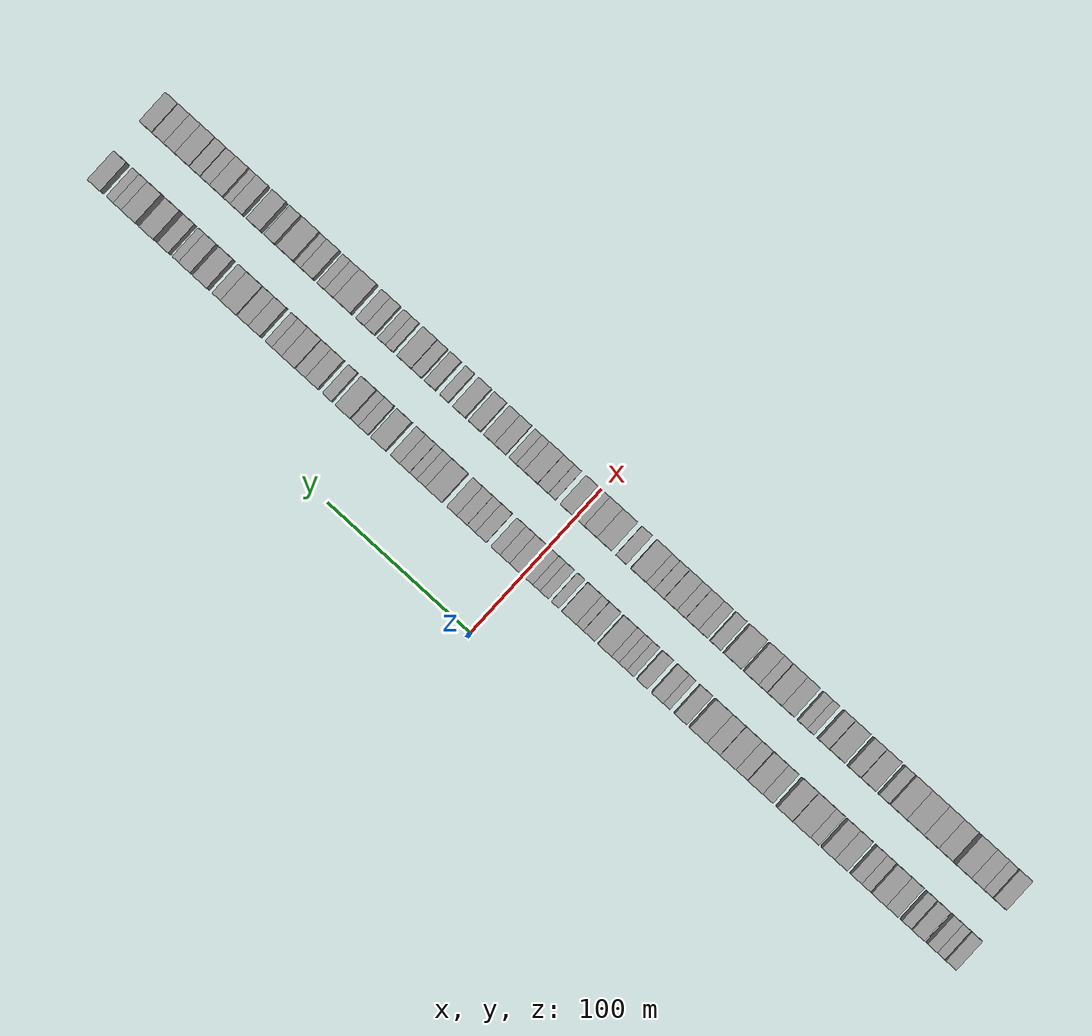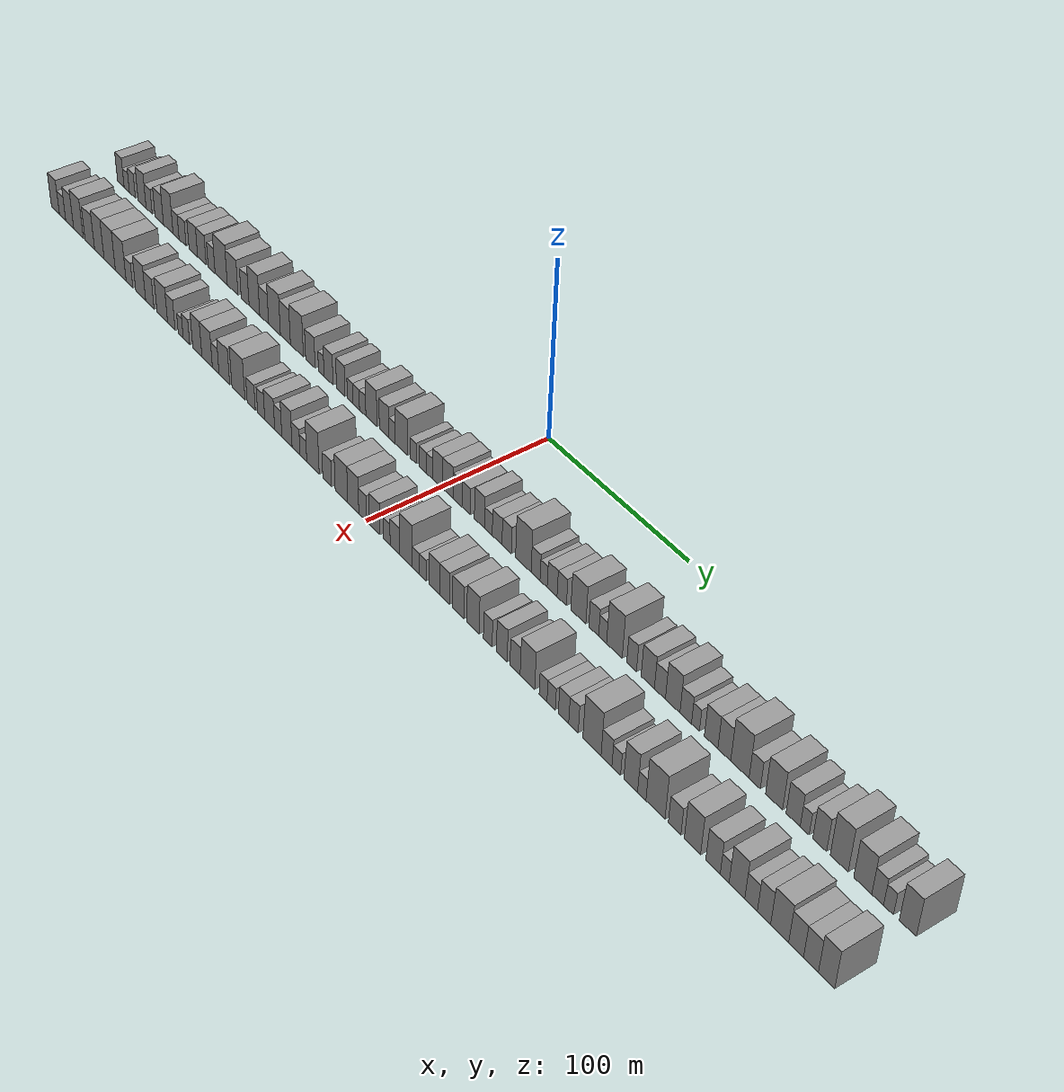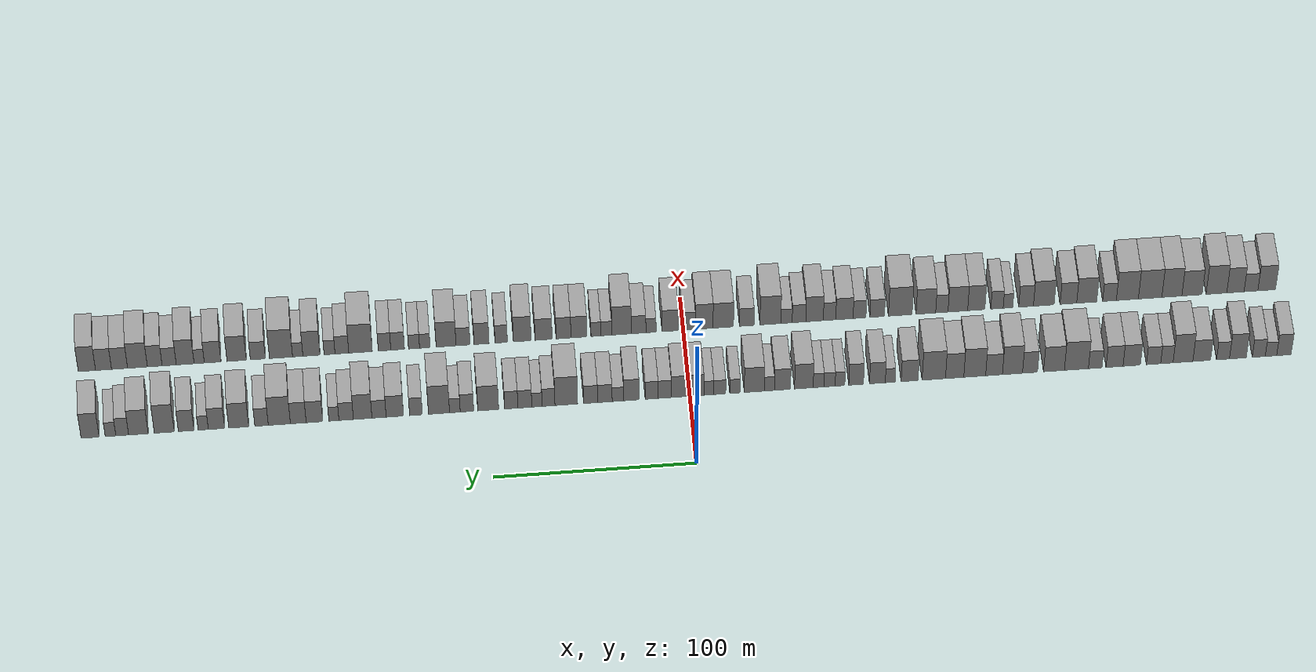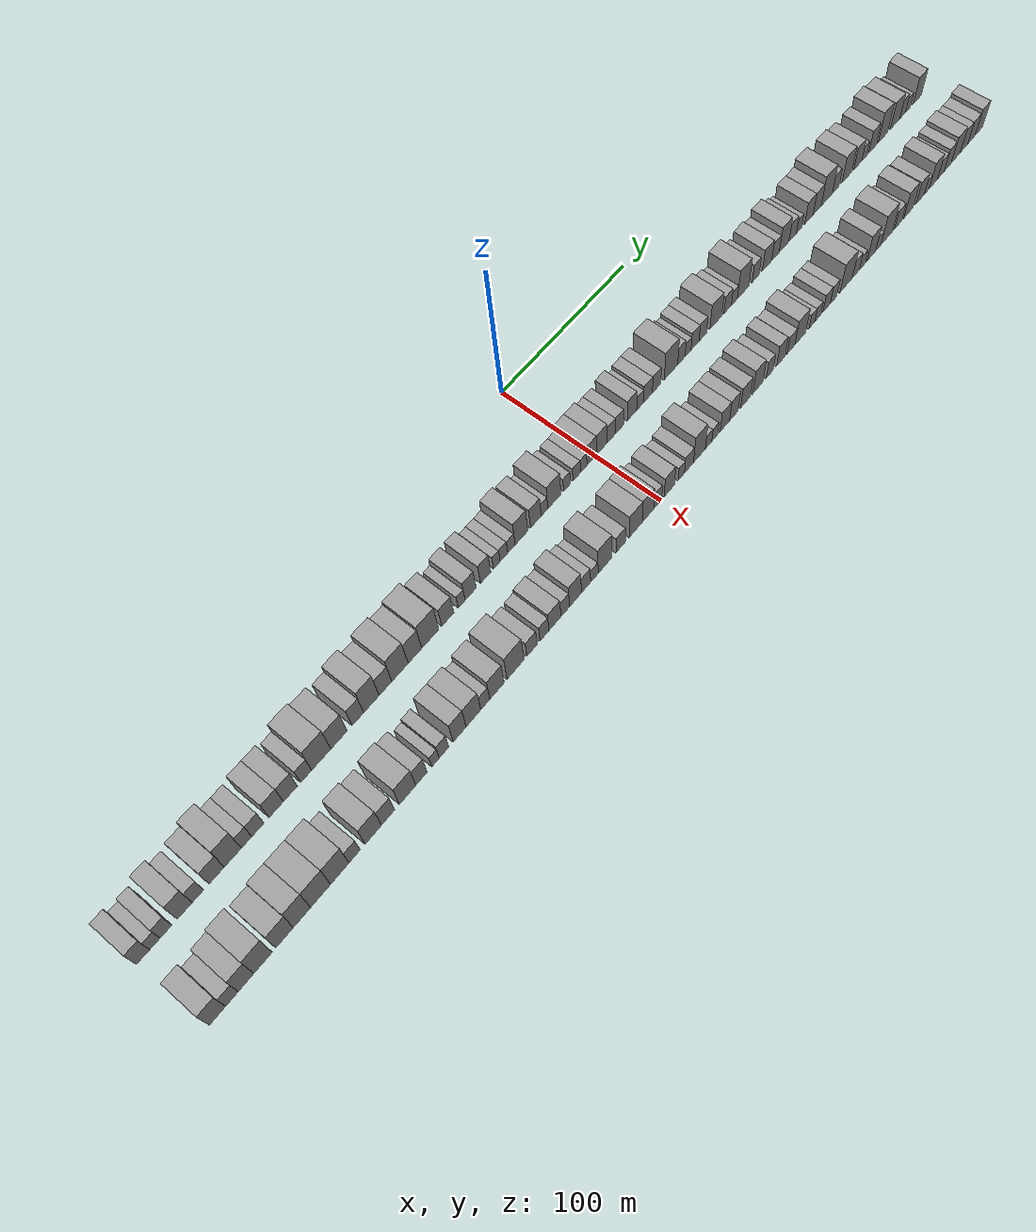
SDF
<sdf version="1.6">
 <world name="default">
  <scene>
   <sky><clouds><speed>12</speed></clouds></sky>
   <ambient>0.4 0.4 0.4 1</ambient>
   <background>0.7 0.7 0.7 1</background>
   <shadows>1</shadows>
  </scene>
  <gravity>0 0 -9.8066</gravity>
  <magnetic_field>6e-06 2.3e-05 -4.2e-05</magnetic_field>
  <physics default="0" name="default_physics" type="ode">
   <ode>
    <solver>
     <type>quick</type>
     <iters>10</iters>
     <sor>1.0</sor>
     <use_dynamic_moi_rescaling>0</use_dynamic_moi_rescaling>
    </solver>
    <constraints>
     <cfm>0</cfm>
     <erp>0.2</erp>
     <contact_max_correcting_vel>100</contact_max_correcting_vel>
     <contact_surface_layer>0.001</contact_surface_layer>
    </constraints>
   </ode>
   <max_step_size>0.004</max_step_size>
   <real_time_factor>1</real_time_factor>
   <real_time_update_rate>250</real_time_update_rate>
  </physics>
  <light name="sun" type="directional">
   <pose>0 0 10 0 0 0</pose>
   <diffuse>0.8 0.8 0.8 1</diffuse>
   <specular>0.2 0.2 0.2 1</specular>
   <attenuation>
    <range>1000</range>
    <constant>0.9</constant>
    <linear>0.01</linear>
    <quadratic>0.001</quadratic>
   </attenuation>
   <direction>-0.5 0.1 -0.9</direction>
  </light>
  <model name="building_1">
   <static>1</static>
   <pose>50.0000 -296.3938 0 0.000000 0.000000 0.000000</pose>
   <link name="link">
    <pose>0 0 9.00 0 0 0</pose>
    <collision name="collision"><geometry><box><size>20.0000 7.2124 18.0000</size></box></geometry></collision>
    <visual name="visual">
     <cast_shadows>0</cast_shadows>
     <geometry><box><size>20.0000 7.2124 18.0000</size></box></geometry>
     <material>
      <script>
       <uri>model://grey_wall/materials/scripts</uri>
       <uri>model://grey_wall/materials/textures</uri>
       <name>vrc/grey_wall</name>
      </script>
     </material>
    </visual>
   </link>
  </model>
  <model name="building_2">
   <static>1</static>
   <pose>50.0000 -289.9221 0 0.000000 0.000000 0.000000</pose>
   <link name="link">
    <pose>0 0 6.00 0 0 0</pose>
    <collision name="collision"><geometry><box><size>20.0000 5.7311 12.0000</size></box></geometry></collision>
    <visual name="visual">
     <cast_shadows>0</cast_shadows>
     <geometry><box><size>20.0000 5.7311 12.0000</size></box></geometry>
     <material>
      <script>
       <uri>model://grey_wall/materials/scripts</uri>
       <uri>model://grey_wall/materials/textures</uri>
       <name>vrc/grey_wall</name>
      </script>
     </material>
    </visual>
   </link>
  </model>
  <model name="building_3">
   <static>1</static>
   <pose>50.0000 -283.7980 0 0.000000 0.000000 0.000000</pose>
   <link name="link">
    <pose>0 0 7.50 0 0 0</pose>
    <collision name="collision"><geometry><box><size>20.0000 6.5171 15.0000</size></box></geometry></collision>
    <visual name="visual">
     <cast_shadows>0</cast_shadows>
     <geometry><box><size>20.0000 6.5171 15.0000</size></box></geometry>
     <material>
      <script>
       <uri>model://grey_wall/materials/scripts</uri>
       <uri>model://grey_wall/materials/textures</uri>
       <name>vrc/grey_wall</name>
      </script>
     </material>
    </visual>
   </link>
  </model>
  <model name="building_4">
   <static>1</static>
   <pose>50.0000 -273.3251 0 0.000000 0.000000 0.000000</pose>
   <link name="link">
    <pose>0 0 10.50 0 0 0</pose>
    <collision name="collision"><geometry><box><size>20.0000 8.4287 21.0000</size></box></geometry></collision>
    <visual name="visual">
     <cast_shadows>0</cast_shadows>
     <geometry><box><size>20.0000 8.4287 21.0000</size></box></geometry>
     <material>
      <script>
       <uri>model://grey_wall/materials/scripts</uri>
       <uri>model://grey_wall/materials/textures</uri>
       <name>vrc/grey_wall</name>
      </script>
     </material>
    </visual>
   </link>
  </model>
  <model name="building_5">
   <static>1</static>
   <pose>50.0000 -265.8694 0 0.000000 0.000000 0.000000</pose>
   <link name="link">
    <pose>0 0 7.50 0 0 0</pose>
    <collision name="collision"><geometry><box><size>20.0000 6.4827 15.0000</size></box></geometry></collision>
    <visual name="visual">
     <cast_shadows>0</cast_shadows>
     <geometry><box><size>20.0000 6.4827 15.0000</size></box></geometry>
     <material>
      <script>
       <uri>model://grey_wall/materials/scripts</uri>
       <uri>model://grey_wall/materials/textures</uri>
       <name>vrc/grey_wall</name>
      </script>
     </material>
    </visual>
   </link>
  </model>
  <model name="building_6">
   <static>1</static>
   <pose>50.0000 -255.1822 0 0.000000 0.000000 0.000000</pose>
   <link name="link">
    <pose>0 0 9.00 0 0 0</pose>
    <collision name="collision"><geometry><box><size>20.0000 8.8916 18.0000</size></box></geometry></collision>
    <visual name="visual">
     <cast_shadows>0</cast_shadows>
     <geometry><box><size>20.0000 8.8916 18.0000</size></box></geometry>
     <material>
      <script>
       <uri>model://grey_wall/materials/scripts</uri>
       <uri>model://grey_wall/materials/textures</uri>
       <name>vrc/grey_wall</name>
      </script>
     </material>
    </visual>
   </link>
  </model>
  <model name="building_7">
   <static>1</static>
   <pose>50.0000 -245.7802 0 0.000000 0.000000 0.000000</pose>
   <link name="link">
    <pose>0 0 12.00 0 0 0</pose>
    <collision name="collision"><geometry><box><size>20.0000 9.9125 24.0000</size></box></geometry></collision>
    <visual name="visual">
     <cast_shadows>0</cast_shadows>
     <geometry><box><size>20.0000 9.9125 24.0000</size></box></geometry>
     <material>
      <script>
       <uri>model://grey_wall/materials/scripts</uri>
       <uri>model://grey_wall/materials/textures</uri>
       <name>vrc/grey_wall</name>
      </script>
     </material>
    </visual>
   </link>
  </model>
  <model name="building_8">
   <static>1</static>
   <pose>50.0000 -237.7460 0 0.000000 0.000000 0.000000</pose>
   <link name="link">
    <pose>0 0 7.50 0 0 0</pose>
    <collision name="collision"><geometry><box><size>20.0000 6.1559 15.0000</size></box></geometry></collision>
    <visual name="visual">
     <cast_shadows>0</cast_shadows>
     <geometry><box><size>20.0000 6.1559 15.0000</size></box></geometry>
     <material>
      <script>
       <uri>model://grey_wall/materials/scripts</uri>
       <uri>model://grey_wall/materials/textures</uri>
       <name>vrc/grey_wall</name>
      </script>
     </material>
    </visual>
   </link>
  </model>
  <model name="building_9">
   <static>1</static>
   <pose>50.0000 -231.0700 0 0.000000 0.000000 0.000000</pose>
   <link name="link">
    <pose>0 0 7.50 0 0 0</pose>
    <collision name="collision"><geometry><box><size>20.0000 7.1961 15.0000</size></box></geometry></collision>
    <visual name="visual">
     <cast_shadows>0</cast_shadows>
     <geometry><box><size>20.0000 7.1961 15.0000</size></box></geometry>
     <material>
      <script>
       <uri>model://grey_wall/materials/scripts</uri>
       <uri>model://grey_wall/materials/textures</uri>
       <name>vrc/grey_wall</name>
      </script>
     </material>
    </visual>
   </link>
  </model>
  <model name="building_10">
   <static>1</static>
   <pose>50.0000 -220.1311 0 0.000000 0.000000 0.000000</pose>
   <link name="link">
    <pose>0 0 9.00 0 0 0</pose>
    <collision name="collision"><geometry><box><size>20.0000 8.6818 18.0000</size></box></geometry></collision>
    <visual name="visual">
     <cast_shadows>0</cast_shadows>
     <geometry><box><size>20.0000 8.6818 18.0000</size></box></geometry>
     <material>
      <script>
       <uri>model://grey_wall/materials/scripts</uri>
       <uri>model://grey_wall/materials/textures</uri>
       <name>vrc/grey_wall</name>
      </script>
     </material>
    </visual>
   </link>
  </model>
  <model name="building_11">
   <static>1</static>
   <pose>50.0000 -211.5298 0 0.000000 0.000000 0.000000</pose>
   <link name="link">
    <pose>0 0 9.00 0 0 0</pose>
    <collision name="collision"><geometry><box><size>20.0000 8.5208 18.0000</size></box></geometry></collision>
    <visual name="visual">
     <cast_shadows>0</cast_shadows>
     <geometry><box><size>20.0000 8.5208 18.0000</size></box></geometry>
     <material>
      <script>
       <uri>model://grey_wall/materials/scripts</uri>
       <uri>model://grey_wall/materials/textures</uri>
       <name>vrc/grey_wall</name>
      </script>
     </material>
    </visual>
   </link>
  </model>
  <model name="building_12">
   <static>1</static>
   <pose>50.0000 -201.8621 0 0.000000 0.000000 0.000000</pose>
   <link name="link">
    <pose>0 0 7.50 0 0 0</pose>
    <collision name="collision"><geometry><box><size>20.0000 6.8145 15.0000</size></box></geometry></collision>
    <visual name="visual">
     <cast_shadows>0</cast_shadows>
     <geometry><box><size>20.0000 6.8145 15.0000</size></box></geometry>
     <material>
      <script>
       <uri>model://grey_wall/materials/scripts</uri>
       <uri>model://grey_wall/materials/textures</uri>
       <name>vrc/grey_wall</name>
      </script>
     </material>
    </visual>
   </link>
  </model>
  <model name="building_13">
   <static>1</static>
   <pose>50.0000 -192.4567 0 0.000000 0.000000 0.000000</pose>
   <link name="link">
    <pose>0 0 12.00 0 0 0</pose>
    <collision name="collision"><geometry><box><size>20.0000 11.9965 24.0000</size></box></geometry></collision>
    <visual name="visual">
     <cast_shadows>0</cast_shadows>
     <geometry><box><size>20.0000 11.9965 24.0000</size></box></geometry>
     <material>
      <script>
       <uri>model://grey_wall/materials/scripts</uri>
       <uri>model://grey_wall/materials/textures</uri>
       <name>vrc/grey_wall</name>
      </script>
     </material>
    </visual>
   </link>
  </model>
  <model name="building_14">
   <static>1</static>
   <pose>50.0000 -181.2422 0 0.000000 0.000000 0.000000</pose>
   <link name="link">
    <pose>0 0 10.50 0 0 0</pose>
    <collision name="collision"><geometry><box><size>20.0000 10.4326 21.0000</size></box></geometry></collision>
    <visual name="visual">
     <cast_shadows>0</cast_shadows>
     <geometry><box><size>20.0000 10.4326 21.0000</size></box></geometry>
     <material>
      <script>
       <uri>model://grey_wall/materials/scripts</uri>
       <uri>model://grey_wall/materials/textures</uri>
       <name>vrc/grey_wall</name>
      </script>
     </material>
    </visual>
   </link>
  </model>
  <model name="building_15">
   <static>1</static>
   <pose>50.0000 -169.2734 0 0.000000 0.000000 0.000000</pose>
   <link name="link">
    <pose>0 0 9.00 0 0 0</pose>
    <collision name="collision"><geometry><box><size>20.0000 7.5050 18.0000</size></box></geometry></collision>
    <visual name="visual">
     <cast_shadows>0</cast_shadows>
     <geometry><box><size>20.0000 7.5050 18.0000</size></box></geometry>
     <material>
      <script>
       <uri>model://grey_wall/materials/scripts</uri>
       <uri>model://grey_wall/materials/textures</uri>
       <name>vrc/grey_wall</name>
      </script>
     </material>
    </visual>
   </link>
  </model>
  <model name="building_16">
   <static>1</static>
   <pose>50.0000 -160.4951 0 0.000000 0.000000 0.000000</pose>
   <link name="link">
    <pose>0 0 12.00 0 0 0</pose>
    <collision name="collision"><geometry><box><size>20.0000 10.0514 24.0000</size></box></geometry></collision>
    <visual name="visual">
     <cast_shadows>0</cast_shadows>
     <geometry><box><size>20.0000 10.0514 24.0000</size></box></geometry>
     <material>
      <script>
       <uri>model://grey_wall/materials/scripts</uri>
       <uri>model://grey_wall/materials/textures</uri>
       <name>vrc/grey_wall</name>
      </script>
     </material>
    </visual>
   </link>
  </model>
  <model name="building_17">
   <static>1</static>
   <pose>50.0000 -151.2914 0 0.000000 0.000000 0.000000</pose>
   <link name="link">
    <pose>0 0 9.00 0 0 0</pose>
    <collision name="collision"><geometry><box><size>20.0000 8.3562 18.0000</size></box></geometry></collision>
    <visual name="visual">
     <cast_shadows>0</cast_shadows>
     <geometry><box><size>20.0000 8.3562 18.0000</size></box></geometry>
     <material>
      <script>
       <uri>model://grey_wall/materials/scripts</uri>
       <uri>model://grey_wall/materials/textures</uri>
       <name>vrc/grey_wall</name>
      </script>
     </material>
    </visual>
   </link>
  </model>
  <model name="building_18">
   <static>1</static>
   <pose>50.0000 -141.6628 0 0.000000 0.000000 0.000000</pose>
   <link name="link">
    <pose>0 0 12.00 0 0 0</pose>
    <collision name="collision"><geometry><box><size>20.0000 10.9010 24.0000</size></box></geometry></collision>
    <visual name="visual">
     <cast_shadows>0</cast_shadows>
     <geometry><box><size>20.0000 10.9010 24.0000</size></box></geometry>
     <material>
      <script>
       <uri>model://grey_wall/materials/scripts</uri>
       <uri>model://grey_wall/materials/textures</uri>
       <name>vrc/grey_wall</name>
      </script>
     </material>
    </visual>
   </link>
  </model>
  <model name="building_19">
   <static>1</static>
   <pose>50.0000 -131.6414 0 0.000000 0.000000 0.000000</pose>
   <link name="link">
    <pose>0 0 10.50 0 0 0</pose>
    <collision name="collision"><geometry><box><size>20.0000 9.1419 21.0000</size></box></geometry></collision>
    <visual name="visual">
     <cast_shadows>0</cast_shadows>
     <geometry><box><size>20.0000 9.1419 21.0000</size></box></geometry>
     <material>
      <script>
       <uri>model://grey_wall/materials/scripts</uri>
       <uri>model://grey_wall/materials/textures</uri>
       <name>vrc/grey_wall</name>
      </script>
     </material>
    </visual>
   </link>
  </model>
  <model name="building_20">
   <static>1</static>
   <pose>50.0000 -121.2300 0 0.000000 0.000000 0.000000</pose>
   <link name="link">
    <pose>0 0 12.00 0 0 0</pose>
    <collision name="collision"><geometry><box><size>20.0000 11.6808 24.0000</size></box></geometry></collision>
    <visual name="visual">
     <cast_shadows>0</cast_shadows>
     <geometry><box><size>20.0000 11.6808 24.0000</size></box></geometry>
     <material>
      <script>
       <uri>model://grey_wall/materials/scripts</uri>
       <uri>model://grey_wall/materials/textures</uri>
       <name>vrc/grey_wall</name>
      </script>
     </material>
    </visual>
   </link>
  </model>
  <model name="building_21">
   <static>1</static>
   <pose>50.0000 -109.1669 0 0.000000 0.000000 0.000000</pose>
   <link name="link">
    <pose>0 0 9.00 0 0 0</pose>
    <collision name="collision"><geometry><box><size>20.0000 8.4455 18.0000</size></box></geometry></collision>
    <visual name="visual">
     <cast_shadows>0</cast_shadows>
     <geometry><box><size>20.0000 8.4455 18.0000</size></box></geometry>
     <material>
      <script>
       <uri>model://grey_wall/materials/scripts</uri>
       <uri>model://grey_wall/materials/textures</uri>
       <name>vrc/grey_wall</name>
      </script>
     </material>
    </visual>
   </link>
  </model>
  <model name="building_22">
   <static>1</static>
   <pose>50.0000 -99.4959 0 0.000000 0.000000 0.000000</pose>
   <link name="link">
    <pose>0 0 6.00 0 0 0</pose>
    <collision name="collision"><geometry><box><size>20.0000 4.8965 12.0000</size></box></geometry></collision>
    <visual name="visual">
     <cast_shadows>0</cast_shadows>
     <geometry><box><size>20.0000 4.8965 12.0000</size></box></geometry>
     <material>
      <script>
       <uri>model://grey_wall/materials/scripts</uri>
       <uri>model://grey_wall/materials/textures</uri>
       <name>vrc/grey_wall</name>
      </script>
     </material>
    </visual>
   </link>
  </model>
  <model name="building_23">
   <static>1</static>
   <pose>50.0000 -93.1157 0 0.000000 0.000000 0.000000</pose>
   <link name="link">
    <pose>0 0 9.00 0 0 0</pose>
    <collision name="collision"><geometry><box><size>20.0000 7.8640 18.0000</size></box></geometry></collision>
    <visual name="visual">
     <cast_shadows>0</cast_shadows>
     <geometry><box><size>20.0000 7.8640 18.0000</size></box></geometry>
     <material>
      <script>
       <uri>model://grey_wall/materials/scripts</uri>
       <uri>model://grey_wall/materials/textures</uri>
       <name>vrc/grey_wall</name>
      </script>
     </material>
    </visual>
   </link>
  </model>
  <model name="building_24">
   <static>1</static>
   <pose>50.0000 -82.5297 0 0.000000 0.000000 0.000000</pose>
   <link name="link">
    <pose>0 0 9.00 0 0 0</pose>
    <collision name="collision"><geometry><box><size>20.0000 7.3079 18.0000</size></box></geometry></collision>
    <visual name="visual">
     <cast_shadows>0</cast_shadows>
     <geometry><box><size>20.0000 7.3079 18.0000</size></box></geometry>
     <material>
      <script>
       <uri>model://grey_wall/materials/scripts</uri>
       <uri>model://grey_wall/materials/textures</uri>
       <name>vrc/grey_wall</name>
      </script>
     </material>
    </visual>
   </link>
  </model>
  <model name="building_25">
   <static>1</static>
   <pose>50.0000 -74.4745 0 0.000000 0.000000 0.000000</pose>
   <link name="link">
    <pose>0 0 6.00 0 0 0</pose>
    <collision name="collision"><geometry><box><size>20.0000 4.8025 12.0000</size></box></geometry></collision>
    <visual name="visual">
     <cast_shadows>0</cast_shadows>
     <geometry><box><size>20.0000 4.8025 12.0000</size></box></geometry>
     <material>
      <script>
       <uri>model://grey_wall/materials/scripts</uri>
       <uri>model://grey_wall/materials/textures</uri>
       <name>vrc/grey_wall</name>
      </script>
     </material>
    </visual>
   </link>
  </model>
  <model name="building_26">
   <static>1</static>
   <pose>50.0000 -69.2861 0 0.000000 0.000000 0.000000</pose>
   <link name="link">
    <pose>0 0 6.00 0 0 0</pose>
    <collision name="collision"><geometry><box><size>20.0000 5.5743 12.0000</size></box></geometry></collision>
    <visual name="visual">
     <cast_shadows>0</cast_shadows>
     <geometry><box><size>20.0000 5.5743 12.0000</size></box></geometry>
     <material>
      <script>
       <uri>model://grey_wall/materials/scripts</uri>
       <uri>model://grey_wall/materials/textures</uri>
       <name>vrc/grey_wall</name>
      </script>
     </material>
    </visual>
   </link>
  </model>
  <model name="building_27">
   <static>1</static>
   <pose>50.0000 -63.8229 0 0.000000 0.000000 0.000000</pose>
   <link name="link">
    <pose>0 0 6.00 0 0 0</pose>
    <collision name="collision"><geometry><box><size>20.0000 5.3521 12.0000</size></box></geometry></collision>
    <visual name="visual">
     <cast_shadows>0</cast_shadows>
     <geometry><box><size>20.0000 5.3521 12.0000</size></box></geometry>
     <material>
      <script>
       <uri>model://grey_wall/materials/scripts</uri>
       <uri>model://grey_wall/materials/textures</uri>
       <name>vrc/grey_wall</name>
      </script>
     </material>
    </visual>
   </link>
  </model>
  <model name="building_28">
   <static>1</static>
   <pose>50.0000 -56.4965 0 0.000000 0.000000 0.000000</pose>
   <link name="link">
    <pose>0 0 10.50 0 0 0</pose>
    <collision name="collision"><geometry><box><size>20.0000 9.3006 21.0000</size></box></geometry></collision>
    <visual name="visual">
     <cast_shadows>0</cast_shadows>
     <geometry><box><size>20.0000 9.3006 21.0000</size></box></geometry>
     <material>
      <script>
       <uri>model://grey_wall/materials/scripts</uri>
       <uri>model://grey_wall/materials/textures</uri>
       <name>vrc/grey_wall</name>
      </script>
     </material>
    </visual>
   </link>
  </model>
  <model name="building_29">
   <static>1</static>
   <pose>50.0000 -45.8440 0 0.000000 0.000000 0.000000</pose>
   <link name="link">
    <pose>0 0 9.00 0 0 0</pose>
    <collision name="collision"><geometry><box><size>20.0000 8.0045 18.0000</size></box></geometry></collision>
    <visual name="visual">
     <cast_shadows>0</cast_shadows>
     <geometry><box><size>20.0000 8.0045 18.0000</size></box></geometry>
     <material>
      <script>
       <uri>model://grey_wall/materials/scripts</uri>
       <uri>model://grey_wall/materials/textures</uri>
       <name>vrc/grey_wall</name>
      </script>
     </material>
    </visual>
   </link>
  </model>
  <model name="building_30">
   <static>1</static>
   <pose>50.0000 -39.3203 0 0.000000 0.000000 0.000000</pose>
   <link name="link">
    <pose>0 0 6.00 0 0 0</pose>
    <collision name="collision"><geometry><box><size>20.0000 5.0430 12.0000</size></box></geometry></collision>
    <visual name="visual">
     <cast_shadows>0</cast_shadows>
     <geometry><box><size>20.0000 5.0430 12.0000</size></box></geometry>
     <material>
      <script>
       <uri>model://grey_wall/materials/scripts</uri>
       <uri>model://grey_wall/materials/textures</uri>
       <name>vrc/grey_wall</name>
      </script>
     </material>
    </visual>
   </link>
  </model>
  <model name="building_31">
   <static>1</static>
   <pose>50.0000 -31.8423 0 0.000000 0.000000 0.000000</pose>
   <link name="link">
    <pose>0 0 10.50 0 0 0</pose>
    <collision name="collision"><geometry><box><size>20.0000 9.9128 21.0000</size></box></geometry></collision>
    <visual name="visual">
     <cast_shadows>0</cast_shadows>
     <geometry><box><size>20.0000 9.9128 21.0000</size></box></geometry>
     <material>
      <script>
       <uri>model://grey_wall/materials/scripts</uri>
       <uri>model://grey_wall/materials/textures</uri>
       <name>vrc/grey_wall</name>
      </script>
     </material>
    </visual>
   </link>
  </model>
  <model name="building_32">
   <static>1</static>
   <pose>50.0000 -22.2668 0 0.000000 0.000000 0.000000</pose>
   <link name="link">
    <pose>0 0 6.00 0 0 0</pose>
    <collision name="collision"><geometry><box><size>20.0000 5.2384 12.0000</size></box></geometry></collision>
    <visual name="visual">
     <cast_shadows>0</cast_shadows>
     <geometry><box><size>20.0000 5.2384 12.0000</size></box></geometry>
     <material>
      <script>
       <uri>model://grey_wall/materials/scripts</uri>
       <uri>model://grey_wall/materials/textures</uri>
       <name>vrc/grey_wall</name>
      </script>
     </material>
    </visual>
   </link>
  </model>
  <model name="building_33">
   <static>1</static>
   <pose>50.0000 -14.6996 0 0.000000 0.000000 0.000000</pose>
   <link name="link">
    <pose>0 0 6.00 0 0 0</pose>
    <collision name="collision"><geometry><box><size>20.0000 5.8960 12.0000</size></box></geometry></collision>
    <visual name="visual">
     <cast_shadows>0</cast_shadows>
     <geometry><box><size>20.0000 5.8960 12.0000</size></box></geometry>
     <material>
      <script>
       <uri>model://grey_wall/materials/scripts</uri>
       <uri>model://grey_wall/materials/textures</uri>
       <name>vrc/grey_wall</name>
      </script>
     </material>
    </visual>
   </link>
  </model>
  <model name="building_34">
   <static>1</static>
   <pose>50.0000 -9.2656 0 0.000000 0.000000 0.000000</pose>
   <link name="link">
    <pose>0 0 6.00 0 0 0</pose>
    <collision name="collision"><geometry><box><size>20.0000 4.9720 12.0000</size></box></geometry></collision>
    <visual name="visual">
     <cast_shadows>0</cast_shadows>
     <geometry><box><size>20.0000 4.9720 12.0000</size></box></geometry>
     <material>
      <script>
       <uri>model://grey_wall/materials/scripts</uri>
       <uri>model://grey_wall/materials/textures</uri>
       <name>vrc/grey_wall</name>
      </script>
     </material>
    </visual>
   </link>
  </model>
  <model name="building_35">
   <static>1</static>
   <pose>50.0000 -2.9061 0 0.000000 0.000000 0.000000</pose>
   <link name="link">
    <pose>0 0 9.00 0 0 0</pose>
    <collision name="collision"><geometry><box><size>20.0000 7.7469 18.0000</size></box></geometry></collision>
    <visual name="visual">
     <cast_shadows>0</cast_shadows>
     <geometry><box><size>20.0000 7.7469 18.0000</size></box></geometry>
     <material>
      <script>
       <uri>model://grey_wall/materials/scripts</uri>
       <uri>model://grey_wall/materials/textures</uri>
       <name>vrc/grey_wall</name>
      </script>
     </material>
    </visual>
   </link>
  </model>
  <model name="building_36">
   <static>1</static>
   <pose>50.0000 5.1324 0 0.000000 0.000000 0.000000</pose>
   <link name="link">
    <pose>0 0 9.00 0 0 0</pose>
    <collision name="collision"><geometry><box><size>20.0000 8.3301 18.0000</size></box></geometry></collision>
    <visual name="visual">
     <cast_shadows>0</cast_shadows>
     <geometry><box><size>20.0000 8.3301 18.0000</size></box></geometry>
     <material>
      <script>
       <uri>model://grey_wall/materials/scripts</uri>
       <uri>model://grey_wall/materials/textures</uri>
       <name>vrc/grey_wall</name>
      </script>
     </material>
    </visual>
   </link>
  </model>
  <model name="building_37">
   <static>1</static>
   <pose>50.0000 12.5911 0 0.000000 0.000000 0.000000</pose>
   <link name="link">
    <pose>0 0 7.50 0 0 0</pose>
    <collision name="collision"><geometry><box><size>20.0000 6.5872 15.0000</size></box></geometry></collision>
    <visual name="visual">
     <cast_shadows>0</cast_shadows>
     <geometry><box><size>20.0000 6.5872 15.0000</size></box></geometry>
     <material>
      <script>
       <uri>model://grey_wall/materials/scripts</uri>
       <uri>model://grey_wall/materials/textures</uri>
       <name>vrc/grey_wall</name>
      </script>
     </material>
    </visual>
   </link>
  </model>
  <model name="building_38">
   <static>1</static>
   <pose>50.0000 19.1160 0 0.000000 0.000000 0.000000</pose>
   <link name="link">
    <pose>0 0 7.50 0 0 0</pose>
    <collision name="collision"><geometry><box><size>20.0000 6.4626 15.0000</size></box></geometry></collision>
    <visual name="visual">
     <cast_shadows>0</cast_shadows>
     <geometry><box><size>20.0000 6.4626 15.0000</size></box></geometry>
     <material>
      <script>
       <uri>model://grey_wall/materials/scripts</uri>
       <uri>model://grey_wall/materials/textures</uri>
       <name>vrc/grey_wall</name>
      </script>
     </material>
    </visual>
   </link>
  </model>
  <model name="building_39">
   <static>1</static>
   <pose>50.0000 29.1546 0 0.000000 0.000000 0.000000</pose>
   <link name="link">
    <pose>0 0 9.00 0 0 0</pose>
    <collision name="collision"><geometry><box><size>20.0000 7.6145 18.0000</size></box></geometry></collision>
    <visual name="visual">
     <cast_shadows>0</cast_shadows>
     <geometry><box><size>20.0000 7.6145 18.0000</size></box></geometry>
     <material>
      <script>
       <uri>model://grey_wall/materials/scripts</uri>
       <uri>model://grey_wall/materials/textures</uri>
       <name>vrc/grey_wall</name>
      </script>
     </material>
    </visual>
   </link>
  </model>
  <model name="building_40">
   <static>1</static>
   <pose>50.0000 35.8505 0 0.000000 0.000000 0.000000</pose>
   <link name="link">
    <pose>0 0 6.00 0 0 0</pose>
    <collision name="collision"><geometry><box><size>20.0000 5.7773 12.0000</size></box></geometry></collision>
    <visual name="visual">
     <cast_shadows>0</cast_shadows>
     <geometry><box><size>20.0000 5.7773 12.0000</size></box></geometry>
     <material>
      <script>
       <uri>model://grey_wall/materials/scripts</uri>
       <uri>model://grey_wall/materials/textures</uri>
       <name>vrc/grey_wall</name>
      </script>
     </material>
    </visual>
   </link>
  </model>
  <model name="building_41">
   <static>1</static>
   <pose>50.0000 42.3434 0 0.000000 0.000000 0.000000</pose>
   <link name="link">
    <pose>0 0 7.50 0 0 0</pose>
    <collision name="collision"><geometry><box><size>20.0000 7.2085 15.0000</size></box></geometry></collision>
    <visual name="visual">
     <cast_shadows>0</cast_shadows>
     <geometry><box><size>20.0000 7.2085 15.0000</size></box></geometry>
     <material>
      <script>
       <uri>model://grey_wall/materials/scripts</uri>
       <uri>model://grey_wall/materials/textures</uri>
       <name>vrc/grey_wall</name>
      </script>
     </material>
    </visual>
   </link>
  </model>
  <model name="building_42">
   <static>1</static>
   <pose>50.0000 49.4130 0 0.000000 0.000000 0.000000</pose>
   <link name="link">
    <pose>0 0 7.50 0 0 0</pose>
    <collision name="collision"><geometry><box><size>20.0000 6.9307 15.0000</size></box></geometry></collision>
    <visual name="visual">
     <cast_shadows>0</cast_shadows>
     <geometry><box><size>20.0000 6.9307 15.0000</size></box></geometry>
     <material>
      <script>
       <uri>model://grey_wall/materials/scripts</uri>
       <uri>model://grey_wall/materials/textures</uri>
       <name>vrc/grey_wall</name>
      </script>
     </material>
    </visual>
   </link>
  </model>
  <model name="building_43">
   <static>1</static>
   <pose>50.0000 61.4989 0 0.000000 0.000000 0.000000</pose>
   <link name="link">
    <pose>0 0 12.00 0 0 0</pose>
    <collision name="collision"><geometry><box><size>20.0000 11.2410 24.0000</size></box></geometry></collision>
    <visual name="visual">
     <cast_shadows>0</cast_shadows>
     <geometry><box><size>20.0000 11.2410 24.0000</size></box></geometry>
     <material>
      <script>
       <uri>model://grey_wall/materials/scripts</uri>
       <uri>model://grey_wall/materials/textures</uri>
       <name>vrc/grey_wall</name>
      </script>
     </material>
    </visual>
   </link>
  </model>
  <model name="building_44">
   <static>1</static>
   <pose>50.0000 70.3000 0 0.000000 0.000000 0.000000</pose>
   <link name="link">
    <pose>0 0 7.50 0 0 0</pose>
    <collision name="collision"><geometry><box><size>20.0000 6.3613 15.0000</size></box></geometry></collision>
    <visual name="visual">
     <cast_shadows>0</cast_shadows>
     <geometry><box><size>20.0000 6.3613 15.0000</size></box></geometry>
     <material>
      <script>
       <uri>model://grey_wall/materials/scripts</uri>
       <uri>model://grey_wall/materials/textures</uri>
       <name>vrc/grey_wall</name>
      </script>
     </material>
    </visual>
   </link>
  </model>
  <model name="building_45">
   <static>1</static>
   <pose>50.0000 76.0259 0 0.000000 0.000000 0.000000</pose>
   <link name="link">
    <pose>0 0 6.00 0 0 0</pose>
    <collision name="collision"><geometry><box><size>20.0000 5.0905 12.0000</size></box></geometry></collision>
    <visual name="visual">
     <cast_shadows>0</cast_shadows>
     <geometry><box><size>20.0000 5.0905 12.0000</size></box></geometry>
     <material>
      <script>
       <uri>model://grey_wall/materials/scripts</uri>
       <uri>model://grey_wall/materials/textures</uri>
       <name>vrc/grey_wall</name>
      </script>
     </material>
    </visual>
   </link>
  </model>
  <model name="building_46">
   <static>1</static>
   <pose>50.0000 82.0209 0 0.000000 0.000000 0.000000</pose>
   <link name="link">
    <pose>0 0 7.50 0 0 0</pose>
    <collision name="collision"><geometry><box><size>20.0000 6.8995 15.0000</size></box></geometry></collision>
    <visual name="visual">
     <cast_shadows>0</cast_shadows>
     <geometry><box><size>20.0000 6.8995 15.0000</size></box></geometry>
     <material>
      <script>
       <uri>model://grey_wall/materials/scripts</uri>
       <uri>model://grey_wall/materials/textures</uri>
       <name>vrc/grey_wall</name>
      </script>
     </material>
    </visual>
   </link>
  </model>
  <model name="building_47">
   <static>1</static>
   <pose>50.0000 88.7367 0 0.000000 0.000000 0.000000</pose>
   <link name="link">
    <pose>0 0 7.50 0 0 0</pose>
    <collision name="collision"><geometry><box><size>20.0000 6.5323 15.0000</size></box></geometry></collision>
    <visual name="visual">
     <cast_shadows>0</cast_shadows>
     <geometry><box><size>20.0000 6.5323 15.0000</size></box></geometry>
     <material>
      <script>
       <uri>model://grey_wall/materials/scripts</uri>
       <uri>model://grey_wall/materials/textures</uri>
       <name>vrc/grey_wall</name>
      </script>
     </material>
    </visual>
   </link>
  </model>
  <model name="building_48">
   <static>1</static>
   <pose>50.0000 100.1746 0 0.000000 0.000000 0.000000</pose>
   <link name="link">
    <pose>0 0 10.50 0 0 0</pose>
    <collision name="collision"><geometry><box><size>20.0000 10.3434 21.0000</size></box></geometry></collision>
    <visual name="visual">
     <cast_shadows>0</cast_shadows>
     <geometry><box><size>20.0000 10.3434 21.0000</size></box></geometry>
     <material>
      <script>
       <uri>model://grey_wall/materials/scripts</uri>
       <uri>model://grey_wall/materials/textures</uri>
       <name>vrc/grey_wall</name>
      </script>
     </material>
    </visual>
   </link>
  </model>
  <model name="building_49">
   <static>1</static>
   <pose>50.0000 110.6861 0 0.000000 0.000000 0.000000</pose>
   <link name="link">
    <pose>0 0 7.50 0 0 0</pose>
    <collision name="collision"><geometry><box><size>20.0000 6.6797 15.0000</size></box></geometry></collision>
    <visual name="visual">
     <cast_shadows>0</cast_shadows>
     <geometry><box><size>20.0000 6.6797 15.0000</size></box></geometry>
     <material>
      <script>
       <uri>model://grey_wall/materials/scripts</uri>
       <uri>model://grey_wall/materials/textures</uri>
       <name>vrc/grey_wall</name>
      </script>
     </material>
    </visual>
   </link>
  </model>
  <model name="building_50">
   <static>1</static>
   <pose>50.0000 116.6713 0 0.000000 0.000000 0.000000</pose>
   <link name="link">
    <pose>0 0 6.00 0 0 0</pose>
    <collision name="collision"><geometry><box><size>20.0000 5.2907 12.0000</size></box></geometry></collision>
    <visual name="visual">
     <cast_shadows>0</cast_shadows>
     <geometry><box><size>20.0000 5.2907 12.0000</size></box></geometry>
     <material>
      <script>
       <uri>model://grey_wall/materials/scripts</uri>
       <uri>model://grey_wall/materials/textures</uri>
       <name>vrc/grey_wall</name>
      </script>
     </material>
    </visual>
   </link>
  </model>
  <model name="building_51">
   <static>1</static>
   <pose>50.0000 124.5184 0 0.000000 0.000000 0.000000</pose>
   <link name="link">
    <pose>0 0 12.00 0 0 0</pose>
    <collision name="collision"><geometry><box><size>20.0000 10.4035 24.0000</size></box></geometry></collision>
    <visual name="visual">
     <cast_shadows>0</cast_shadows>
     <geometry><box><size>20.0000 10.4035 24.0000</size></box></geometry>
     <material>
      <script>
       <uri>model://grey_wall/materials/scripts</uri>
       <uri>model://grey_wall/materials/textures</uri>
       <name>vrc/grey_wall</name>
      </script>
     </material>
    </visual>
   </link>
  </model>
  <model name="building_52">
   <static>1</static>
   <pose>50.0000 135.8873 0 0.000000 0.000000 0.000000</pose>
   <link name="link">
    <pose>0 0 7.50 0 0 0</pose>
    <collision name="collision"><geometry><box><size>20.0000 6.3343 15.0000</size></box></geometry></collision>
    <visual name="visual">
     <cast_shadows>0</cast_shadows>
     <geometry><box><size>20.0000 6.3343 15.0000</size></box></geometry>
     <material>
      <script>
       <uri>model://grey_wall/materials/scripts</uri>
       <uri>model://grey_wall/materials/textures</uri>
       <name>vrc/grey_wall</name>
      </script>
     </material>
    </visual>
   </link>
  </model>
  <model name="building_53">
   <static>1</static>
   <pose>50.0000 146.3460 0 0.000000 0.000000 0.000000</pose>
   <link name="link">
    <pose>0 0 9.00 0 0 0</pose>
    <collision name="collision"><geometry><box><size>20.0000 8.5831 18.0000</size></box></geometry></collision>
    <visual name="visual">
     <cast_shadows>0</cast_shadows>
     <geometry><box><size>20.0000 8.5831 18.0000</size></box></geometry>
     <material>
      <script>
       <uri>model://grey_wall/materials/scripts</uri>
       <uri>model://grey_wall/materials/textures</uri>
       <name>vrc/grey_wall</name>
      </script>
     </material>
    </visual>
   </link>
  </model>
  <model name="building_54">
   <static>1</static>
   <pose>50.0000 154.1503 0 0.000000 0.000000 0.000000</pose>
   <link name="link">
    <pose>0 0 7.50 0 0 0</pose>
    <collision name="collision"><geometry><box><size>20.0000 7.0254 15.0000</size></box></geometry></collision>
    <visual name="visual">
     <cast_shadows>0</cast_shadows>
     <geometry><box><size>20.0000 7.0254 15.0000</size></box></geometry>
     <material>
      <script>
       <uri>model://grey_wall/materials/scripts</uri>
       <uri>model://grey_wall/materials/textures</uri>
       <name>vrc/grey_wall</name>
      </script>
     </material>
    </visual>
   </link>
  </model>
  <model name="building_55">
   <static>1</static>
   <pose>50.0000 162.2373 0 0.000000 0.000000 0.000000</pose>
   <link name="link">
    <pose>0 0 10.50 0 0 0</pose>
    <collision name="collision"><geometry><box><size>20.0000 9.1486 21.0000</size></box></geometry></collision>
    <visual name="visual">
     <cast_shadows>0</cast_shadows>
     <geometry><box><size>20.0000 9.1486 21.0000</size></box></geometry>
     <material>
      <script>
       <uri>model://grey_wall/materials/scripts</uri>
       <uri>model://grey_wall/materials/textures</uri>
       <name>vrc/grey_wall</name>
      </script>
     </material>
    </visual>
   </link>
  </model>
  <model name="building_56">
   <static>1</static>
   <pose>50.0000 170.3961 0 0.000000 0.000000 0.000000</pose>
   <link name="link">
    <pose>0 0 7.50 0 0 0</pose>
    <collision name="collision"><geometry><box><size>20.0000 7.1690 15.0000</size></box></geometry></collision>
    <visual name="visual">
     <cast_shadows>0</cast_shadows>
     <geometry><box><size>20.0000 7.1690 15.0000</size></box></geometry>
     <material>
      <script>
       <uri>model://grey_wall/materials/scripts</uri>
       <uri>model://grey_wall/materials/textures</uri>
       <name>vrc/grey_wall</name>
      </script>
     </material>
    </visual>
   </link>
  </model>
  <model name="building_57">
   <static>1</static>
   <pose>50.0000 176.4554 0 0.000000 0.000000 0.000000</pose>
   <link name="link">
    <pose>0 0 6.00 0 0 0</pose>
    <collision name="collision"><geometry><box><size>20.0000 4.9496 12.0000</size></box></geometry></collision>
    <visual name="visual">
     <cast_shadows>0</cast_shadows>
     <geometry><box><size>20.0000 4.9496 12.0000</size></box></geometry>
     <material>
      <script>
       <uri>model://grey_wall/materials/scripts</uri>
       <uri>model://grey_wall/materials/textures</uri>
       <name>vrc/grey_wall</name>
      </script>
     </material>
    </visual>
   </link>
  </model>
  <model name="building_58">
   <static>1</static>
   <pose>50.0000 186.0385 0 0.000000 0.000000 0.000000</pose>
   <link name="link">
    <pose>0 0 9.00 0 0 0</pose>
    <collision name="collision"><geometry><box><size>20.0000 8.2166 18.0000</size></box></geometry></collision>
    <visual name="visual">
     <cast_shadows>0</cast_shadows>
     <geometry><box><size>20.0000 8.2166 18.0000</size></box></geometry>
     <material>
      <script>
       <uri>model://grey_wall/materials/scripts</uri>
       <uri>model://grey_wall/materials/textures</uri>
       <name>vrc/grey_wall</name>
      </script>
     </material>
    </visual>
   </link>
  </model>
  <model name="building_59">
   <static>1</static>
   <pose>50.0000 194.0281 0 0.000000 0.000000 0.000000</pose>
   <link name="link">
    <pose>0 0 9.00 0 0 0</pose>
    <collision name="collision"><geometry><box><size>20.0000 7.7626 18.0000</size></box></geometry></collision>
    <visual name="visual">
     <cast_shadows>0</cast_shadows>
     <geometry><box><size>20.0000 7.7626 18.0000</size></box></geometry>
     <material>
      <script>
       <uri>model://grey_wall/materials/scripts</uri>
       <uri>model://grey_wall/materials/textures</uri>
       <name>vrc/grey_wall</name>
      </script>
     </material>
    </visual>
   </link>
  </model>
  <model name="building_60">
   <static>1</static>
   <pose>50.0000 203.3651 0 0.000000 0.000000 0.000000</pose>
   <link name="link">
    <pose>0 0 12.00 0 0 0</pose>
    <collision name="collision"><geometry><box><size>20.0000 10.9114 24.0000</size></box></geometry></collision>
    <visual name="visual">
     <cast_shadows>0</cast_shadows>
     <geometry><box><size>20.0000 10.9114 24.0000</size></box></geometry>
     <material>
      <script>
       <uri>model://grey_wall/materials/scripts</uri>
       <uri>model://grey_wall/materials/textures</uri>
       <name>vrc/grey_wall</name>
      </script>
     </material>
    </visual>
   </link>
  </model>
  <model name="building_61">
   <static>1</static>
   <pose>50.0000 212.1412 0 0.000000 0.000000 0.000000</pose>
   <link name="link">
    <pose>0 0 7.50 0 0 0</pose>
    <collision name="collision"><geometry><box><size>20.0000 6.6408 15.0000</size></box></geometry></collision>
    <visual name="visual">
     <cast_shadows>0</cast_shadows>
     <geometry><box><size>20.0000 6.6408 15.0000</size></box></geometry>
     <material>
      <script>
       <uri>model://grey_wall/materials/scripts</uri>
       <uri>model://grey_wall/materials/textures</uri>
       <name>vrc/grey_wall</name>
      </script>
     </material>
    </visual>
   </link>
  </model>
  <model name="building_62">
   <static>1</static>
   <pose>50.0000 223.3910 0 0.000000 0.000000 0.000000</pose>
   <link name="link">
    <pose>0 0 10.50 0 0 0</pose>
    <collision name="collision"><geometry><box><size>20.0000 9.8587 21.0000</size></box></geometry></collision>
    <visual name="visual">
     <cast_shadows>0</cast_shadows>
     <geometry><box><size>20.0000 9.8587 21.0000</size></box></geometry>
     <material>
      <script>
       <uri>model://grey_wall/materials/scripts</uri>
       <uri>model://grey_wall/materials/textures</uri>
       <name>vrc/grey_wall</name>
      </script>
     </material>
    </visual>
   </link>
  </model>
  <model name="building_63">
   <static>1</static>
   <pose>50.0000 234.3536 0 0.000000 0.000000 0.000000</pose>
   <link name="link">
    <pose>0 0 9.00 0 0 0</pose>
    <collision name="collision"><geometry><box><size>20.0000 8.0664 18.0000</size></box></geometry></collision>
    <visual name="visual">
     <cast_shadows>0</cast_shadows>
     <geometry><box><size>20.0000 8.0664 18.0000</size></box></geometry>
     <material>
      <script>
       <uri>model://grey_wall/materials/scripts</uri>
       <uri>model://grey_wall/materials/textures</uri>
       <name>vrc/grey_wall</name>
      </script>
     </material>
    </visual>
   </link>
  </model>
  <model name="building_64">
   <static>1</static>
   <pose>50.0000 240.9053 0 0.000000 0.000000 0.000000</pose>
   <link name="link">
    <pose>0 0 6.00 0 0 0</pose>
    <collision name="collision"><geometry><box><size>20.0000 5.0372 12.0000</size></box></geometry></collision>
    <visual name="visual">
     <cast_shadows>0</cast_shadows>
     <geometry><box><size>20.0000 5.0372 12.0000</size></box></geometry>
     <material>
      <script>
       <uri>model://grey_wall/materials/scripts</uri>
       <uri>model://grey_wall/materials/textures</uri>
       <name>vrc/grey_wall</name>
      </script>
     </material>
    </visual>
   </link>
  </model>
  <model name="building_65">
   <static>1</static>
   <pose>50.0000 249.2791 0 0.000000 0.000000 0.000000</pose>
   <link name="link">
    <pose>0 0 9.00 0 0 0</pose>
    <collision name="collision"><geometry><box><size>20.0000 7.7104 18.0000</size></box></geometry></collision>
    <visual name="visual">
     <cast_shadows>0</cast_shadows>
     <geometry><box><size>20.0000 7.7104 18.0000</size></box></geometry>
     <material>
      <script>
       <uri>model://grey_wall/materials/scripts</uri>
       <uri>model://grey_wall/materials/textures</uri>
       <name>vrc/grey_wall</name>
      </script>
     </material>
    </visual>
   </link>
  </model>
  <model name="building_66">
   <static>1</static>
   <pose>50.0000 260.0506 0 0.000000 0.000000 0.000000</pose>
   <link name="link">
    <pose>0 0 12.00 0 0 0</pose>
    <collision name="collision"><geometry><box><size>20.0000 9.8325 24.0000</size></box></geometry></collision>
    <visual name="visual">
     <cast_shadows>0</cast_shadows>
     <geometry><box><size>20.0000 9.8325 24.0000</size></box></geometry>
     <material>
      <script>
       <uri>model://grey_wall/materials/scripts</uri>
       <uri>model://grey_wall/materials/textures</uri>
       <name>vrc/grey_wall</name>
      </script>
     </material>
    </visual>
   </link>
  </model>
  <model name="building_67">
   <static>1</static>
   <pose>50.0000 272.7957 0 0.000000 0.000000 0.000000</pose>
   <link name="link">
    <pose>0 0 10.50 0 0 0</pose>
    <collision name="collision"><geometry><box><size>20.0000 9.6578 21.0000</size></box></geometry></collision>
    <visual name="visual">
     <cast_shadows>0</cast_shadows>
     <geometry><box><size>20.0000 9.6578 21.0000</size></box></geometry>
     <material>
      <script>
       <uri>model://grey_wall/materials/scripts</uri>
       <uri>model://grey_wall/materials/textures</uri>
       <name>vrc/grey_wall</name>
      </script>
     </material>
    </visual>
   </link>
  </model>
  <model name="building_68">
   <static>1</static>
   <pose>50.0000 280.7667 0 0.000000 0.000000 0.000000</pose>
   <link name="link">
    <pose>0 0 7.50 0 0 0</pose>
    <collision name="collision"><geometry><box><size>20.0000 6.2843 15.0000</size></box></geometry></collision>
    <visual name="visual">
     <cast_shadows>0</cast_shadows>
     <geometry><box><size>20.0000 6.2843 15.0000</size></box></geometry>
     <material>
      <script>
       <uri>model://grey_wall/materials/scripts</uri>
       <uri>model://grey_wall/materials/textures</uri>
       <name>vrc/grey_wall</name>
      </script>
     </material>
    </visual>
   </link>
  </model>
  <model name="building_69">
   <static>1</static>
   <pose>50.0000 286.5224 0 0.000000 0.000000 0.000000</pose>
   <link name="link">
    <pose>0 0 6.00 0 0 0</pose>
    <collision name="collision"><geometry><box><size>20.0000 5.2271 12.0000</size></box></geometry></collision>
    <visual name="visual">
     <cast_shadows>0</cast_shadows>
     <geometry><box><size>20.0000 5.2271 12.0000</size></box></geometry>
     <material>
      <script>
       <uri>model://grey_wall/materials/scripts</uri>
       <uri>model://grey_wall/materials/textures</uri>
       <name>vrc/grey_wall</name>
      </script>
     </material>
    </visual>
   </link>
  </model>
  <model name="building_70">
   <static>1</static>
   <pose>50.0000 296.5645 0 0.000000 0.000000 0.000000</pose>
   <link name="link">
    <pose>0 0 10.50 0 0 0</pose>
    <collision name="collision"><geometry><box><size>20.0000 8.8572 21.0000</size></box></geometry></collision>
    <visual name="visual">
     <cast_shadows>0</cast_shadows>
     <geometry><box><size>20.0000 8.8572 21.0000</size></box></geometry>
     <material>
      <script>
       <uri>model://grey_wall/materials/scripts</uri>
       <uri>model://grey_wall/materials/textures</uri>
       <name>vrc/grey_wall</name>
      </script>
     </material>
    </visual>
   </link>
  </model>
  <model name="building_71">
   <static>1</static>
   <pose>90.0000 -293.5367 0 0.000000 0.000000 0.000000</pose>
   <link name="link">
    <pose>0 0 10.50 0 0 0</pose>
    <collision name="collision"><geometry><box><size>20.0000 8.9265 21.0000</size></box></geometry></collision>
    <visual name="visual">
     <cast_shadows>0</cast_shadows>
     <geometry><box><size>20.0000 8.9265 21.0000</size></box></geometry>
     <material>
      <script>
       <uri>model://grey_wall/materials/scripts</uri>
       <uri>model://grey_wall/materials/textures</uri>
       <name>vrc/grey_wall</name>
      </script>
     </material>
    </visual>
   </link>
  </model>
  <model name="building_72">
   <static>1</static>
   <pose>90.0000 -285.5824 0 0.000000 0.000000 0.000000</pose>
   <link name="link">
    <pose>0 0 7.50 0 0 0</pose>
    <collision name="collision"><geometry><box><size>20.0000 6.9822 15.0000</size></box></geometry></collision>
    <visual name="visual">
     <cast_shadows>0</cast_shadows>
     <geometry><box><size>20.0000 6.9822 15.0000</size></box></geometry>
     <material>
      <script>
       <uri>model://grey_wall/materials/scripts</uri>
       <uri>model://grey_wall/materials/textures</uri>
       <name>vrc/grey_wall</name>
      </script>
     </material>
    </visual>
   </link>
  </model>
  <model name="building_73">
   <static>1</static>
   <pose>90.0000 -277.7234 0 0.000000 0.000000 0.000000</pose>
   <link name="link">
    <pose>0 0 10.50 0 0 0</pose>
    <collision name="collision"><geometry><box><size>20.0000 8.7357 21.0000</size></box></geometry></collision>
    <visual name="visual">
     <cast_shadows>0</cast_shadows>
     <geometry><box><size>20.0000 8.7357 21.0000</size></box></geometry>
     <material>
      <script>
       <uri>model://grey_wall/materials/scripts</uri>
       <uri>model://grey_wall/materials/textures</uri>
       <name>vrc/grey_wall</name>
      </script>
     </material>
    </visual>
   </link>
  </model>
  <model name="building_74">
   <static>1</static>
   <pose>90.0000 -268.1141 0 0.000000 0.000000 0.000000</pose>
   <link name="link">
    <pose>0 0 12.00 0 0 0</pose>
    <collision name="collision"><geometry><box><size>20.0000 10.4828 24.0000</size></box></geometry></collision>
    <visual name="visual">
     <cast_shadows>0</cast_shadows>
     <geometry><box><size>20.0000 10.4828 24.0000</size></box></geometry>
     <material>
      <script>
       <uri>model://grey_wall/materials/scripts</uri>
       <uri>model://grey_wall/materials/textures</uri>
       <name>vrc/grey_wall</name>
      </script>
     </material>
    </visual>
   </link>
  </model>
  <model name="building_75">
   <static>1</static>
   <pose>90.0000 -255.7663 0 0.000000 0.000000 0.000000</pose>
   <link name="link">
    <pose>0 0 10.50 0 0 0</pose>
    <collision name="collision"><geometry><box><size>20.0000 10.2129 21.0000</size></box></geometry></collision>
    <visual name="visual">
     <cast_shadows>0</cast_shadows>
     <geometry><box><size>20.0000 10.2129 21.0000</size></box></geometry>
     <material>
      <script>
       <uri>model://grey_wall/materials/scripts</uri>
       <uri>model://grey_wall/materials/textures</uri>
       <name>vrc/grey_wall</name>
      </script>
     </material>
    </visual>
   </link>
  </model>
  <model name="building_76">
   <static>1</static>
   <pose>90.0000 -245.6061 0 0.000000 0.000000 0.000000</pose>
   <link name="link">
    <pose>0 0 12.00 0 0 0</pose>
    <collision name="collision"><geometry><box><size>20.0000 10.1073 24.0000</size></box></geometry></collision>
    <visual name="visual">
     <cast_shadows>0</cast_shadows>
     <geometry><box><size>20.0000 10.1073 24.0000</size></box></geometry>
     <material>
      <script>
       <uri>model://grey_wall/materials/scripts</uri>
       <uri>model://grey_wall/materials/textures</uri>
       <name>vrc/grey_wall</name>
      </script>
     </material>
    </visual>
   </link>
  </model>
  <model name="building_77">
   <static>1</static>
   <pose>90.0000 -234.6219 0 0.000000 0.000000 0.000000</pose>
   <link name="link">
    <pose>0 0 12.00 0 0 0</pose>
    <collision name="collision"><geometry><box><size>20.0000 11.8612 24.0000</size></box></geometry></collision>
    <visual name="visual">
     <cast_shadows>0</cast_shadows>
     <geometry><box><size>20.0000 11.8612 24.0000</size></box></geometry>
     <material>
      <script>
       <uri>model://grey_wall/materials/scripts</uri>
       <uri>model://grey_wall/materials/textures</uri>
       <name>vrc/grey_wall</name>
      </script>
     </material>
    </visual>
   </link>
  </model>
  <model name="building_78">
   <static>1</static>
   <pose>90.0000 -223.1307 0 0.000000 0.000000 0.000000</pose>
   <link name="link">
    <pose>0 0 12.00 0 0 0</pose>
    <collision name="collision"><geometry><box><size>20.0000 11.1212 24.0000</size></box></geometry></collision>
    <visual name="visual">
     <cast_shadows>0</cast_shadows>
     <geometry><box><size>20.0000 11.1212 24.0000</size></box></geometry>
     <material>
      <script>
       <uri>model://grey_wall/materials/scripts</uri>
       <uri>model://grey_wall/materials/textures</uri>
       <name>vrc/grey_wall</name>
      </script>
     </material>
    </visual>
   </link>
  </model>
  <model name="building_79">
   <static>1</static>
   <pose>90.0000 -214.1287 0 0.000000 0.000000 0.000000</pose>
   <link name="link">
    <pose>0 0 7.50 0 0 0</pose>
    <collision name="collision"><geometry><box><size>20.0000 6.8827 15.0000</size></box></geometry></collision>
    <visual name="visual">
     <cast_shadows>0</cast_shadows>
     <geometry><box><size>20.0000 6.8827 15.0000</size></box></geometry>
     <material>
      <script>
       <uri>model://grey_wall/materials/scripts</uri>
       <uri>model://grey_wall/materials/textures</uri>
       <name>vrc/grey_wall</name>
      </script>
     </material>
    </visual>
   </link>
  </model>
  <model name="building_80">
   <static>1</static>
   <pose>90.0000 -202.6399 0 0.000000 0.000000 0.000000</pose>
   <link name="link">
    <pose>0 0 10.50 0 0 0</pose>
    <collision name="collision"><geometry><box><size>20.0000 10.0950 21.0000</size></box></geometry></collision>
    <visual name="visual">
     <cast_shadows>0</cast_shadows>
     <geometry><box><size>20.0000 10.0950 21.0000</size></box></geometry>
     <material>
      <script>
       <uri>model://grey_wall/materials/scripts</uri>
       <uri>model://grey_wall/materials/textures</uri>
       <name>vrc/grey_wall</name>
      </script>
     </material>
    </visual>
   </link>
  </model>
  <model name="building_81">
   <static>1</static>
   <pose>90.0000 -193.3955 0 0.000000 0.000000 0.000000</pose>
   <link name="link">
    <pose>0 0 9.00 0 0 0</pose>
    <collision name="collision"><geometry><box><size>20.0000 8.3936 18.0000</size></box></geometry></collision>
    <visual name="visual">
     <cast_shadows>0</cast_shadows>
     <geometry><box><size>20.0000 8.3936 18.0000</size></box></geometry>
     <material>
      <script>
       <uri>model://grey_wall/materials/scripts</uri>
       <uri>model://grey_wall/materials/textures</uri>
       <name>vrc/grey_wall</name>
      </script>
     </material>
    </visual>
   </link>
  </model>
  <model name="building_82">
   <static>1</static>
   <pose>90.0000 -180.9902 0 0.000000 0.000000 0.000000</pose>
   <link name="link">
    <pose>0 0 10.50 0 0 0</pose>
    <collision name="collision"><geometry><box><size>20.0000 10.4172 21.0000</size></box></geometry></collision>
    <visual name="visual">
     <cast_shadows>0</cast_shadows>
     <geometry><box><size>20.0000 10.4172 21.0000</size></box></geometry>
     <material>
      <script>
       <uri>model://grey_wall/materials/scripts</uri>
       <uri>model://grey_wall/materials/textures</uri>
       <name>vrc/grey_wall</name>
      </script>
     </material>
    </visual>
   </link>
  </model>
  <model name="building_83">
   <static>1</static>
   <pose>90.0000 -172.0745 0 0.000000 0.000000 0.000000</pose>
   <link name="link">
    <pose>0 0 9.00 0 0 0</pose>
    <collision name="collision"><geometry><box><size>20.0000 7.4141 18.0000</size></box></geometry></collision>
    <visual name="visual">
     <cast_shadows>0</cast_shadows>
     <geometry><box><size>20.0000 7.4141 18.0000</size></box></geometry>
     <material>
      <script>
       <uri>model://grey_wall/materials/scripts</uri>
       <uri>model://grey_wall/materials/textures</uri>
       <name>vrc/grey_wall</name>
      </script>
     </material>
    </visual>
   </link>
  </model>
  <model name="building_84">
   <static>1</static>
   <pose>90.0000 -162.9481 0 0.000000 0.000000 0.000000</pose>
   <link name="link">
    <pose>0 0 6.00 0 0 0</pose>
    <collision name="collision"><geometry><box><size>20.0000 4.8387 12.0000</size></box></geometry></collision>
    <visual name="visual">
     <cast_shadows>0</cast_shadows>
     <geometry><box><size>20.0000 4.8387 12.0000</size></box></geometry>
     <material>
      <script>
       <uri>model://grey_wall/materials/scripts</uri>
       <uri>model://grey_wall/materials/textures</uri>
       <name>vrc/grey_wall</name>
      </script>
     </material>
    </visual>
   </link>
  </model>
  <model name="building_85">
   <static>1</static>
   <pose>90.0000 -157.4152 0 0.000000 0.000000 0.000000</pose>
   <link name="link">
    <pose>0 0 7.50 0 0 0</pose>
    <collision name="collision"><geometry><box><size>20.0000 6.2272 15.0000</size></box></geometry></collision>
    <visual name="visual">
     <cast_shadows>0</cast_shadows>
     <geometry><box><size>20.0000 6.2272 15.0000</size></box></geometry>
     <material>
      <script>
       <uri>model://grey_wall/materials/scripts</uri>
       <uri>model://grey_wall/materials/textures</uri>
       <name>vrc/grey_wall</name>
      </script>
     </material>
    </visual>
   </link>
  </model>
  <model name="building_86">
   <static>1</static>
   <pose>90.0000 -146.9797 0 0.000000 0.000000 0.000000</pose>
   <link name="link">
    <pose>0 0 10.50 0 0 0</pose>
    <collision name="collision"><geometry><box><size>20.0000 8.6438 21.0000</size></box></geometry></collision>
    <visual name="visual">
     <cast_shadows>0</cast_shadows>
     <geometry><box><size>20.0000 8.6438 21.0000</size></box></geometry>
     <material>
      <script>
       <uri>model://grey_wall/materials/scripts</uri>
       <uri>model://grey_wall/materials/textures</uri>
       <name>vrc/grey_wall</name>
      </script>
     </material>
    </visual>
   </link>
  </model>
  <model name="building_87">
   <static>1</static>
   <pose>90.0000 -137.7073 0 0.000000 0.000000 0.000000</pose>
   <link name="link">
    <pose>0 0 10.50 0 0 0</pose>
    <collision name="collision"><geometry><box><size>20.0000 9.9009 21.0000</size></box></geometry></collision>
    <visual name="visual">
     <cast_shadows>0</cast_shadows>
     <geometry><box><size>20.0000 9.9009 21.0000</size></box></geometry>
     <material>
      <script>
       <uri>model://grey_wall/materials/scripts</uri>
       <uri>model://grey_wall/materials/textures</uri>
       <name>vrc/grey_wall</name>
      </script>
     </material>
    </visual>
   </link>
  </model>
  <model name="building_88">
   <static>1</static>
   <pose>90.0000 -129.6641 0 0.000000 0.000000 0.000000</pose>
   <link name="link">
    <pose>0 0 7.50 0 0 0</pose>
    <collision name="collision"><geometry><box><size>20.0000 6.1856 15.0000</size></box></geometry></collision>
    <visual name="visual">
     <cast_shadows>0</cast_shadows>
     <geometry><box><size>20.0000 6.1856 15.0000</size></box></geometry>
     <material>
      <script>
       <uri>model://grey_wall/materials/scripts</uri>
       <uri>model://grey_wall/materials/textures</uri>
       <name>vrc/grey_wall</name>
      </script>
     </material>
    </visual>
   </link>
  </model>
  <model name="building_89">
   <static>1</static>
   <pose>90.0000 -121.6349 0 0.000000 0.000000 0.000000</pose>
   <link name="link">
    <pose>0 0 10.50 0 0 0</pose>
    <collision name="collision"><geometry><box><size>20.0000 9.8728 21.0000</size></box></geometry></collision>
    <visual name="visual">
     <cast_shadows>0</cast_shadows>
     <geometry><box><size>20.0000 9.8728 21.0000</size></box></geometry>
     <material>
      <script>
       <uri>model://grey_wall/materials/scripts</uri>
       <uri>model://grey_wall/materials/textures</uri>
       <name>vrc/grey_wall</name>
      </script>
     </material>
    </visual>
   </link>
  </model>
  <model name="building_90">
   <static>1</static>
   <pose>90.0000 -108.7541 0 0.000000 0.000000 0.000000</pose>
   <link name="link">
    <pose>0 0 12.00 0 0 0</pose>
    <collision name="collision"><geometry><box><size>20.0000 11.8887 24.0000</size></box></geometry></collision>
    <visual name="visual">
     <cast_shadows>0</cast_shadows>
     <geometry><box><size>20.0000 11.8887 24.0000</size></box></geometry>
     <material>
      <script>
       <uri>model://grey_wall/materials/scripts</uri>
       <uri>model://grey_wall/materials/textures</uri>
       <name>vrc/grey_wall</name>
      </script>
     </material>
    </visual>
   </link>
  </model>
  <model name="building_91">
   <static>1</static>
   <pose>90.0000 -97.1588 0 0.000000 0.000000 0.000000</pose>
   <link name="link">
    <pose>0 0 7.50 0 0 0</pose>
    <collision name="collision"><geometry><box><size>20.0000 7.3018 15.0000</size></box></geometry></collision>
    <visual name="visual">
     <cast_shadows>0</cast_shadows>
     <geometry><box><size>20.0000 7.3018 15.0000</size></box></geometry>
     <material>
      <script>
       <uri>model://grey_wall/materials/scripts</uri>
       <uri>model://grey_wall/materials/textures</uri>
       <name>vrc/grey_wall</name>
      </script>
     </material>
    </visual>
   </link>
  </model>
  <model name="building_92">
   <static>1</static>
   <pose>90.0000 -88.2832 0 0.000000 0.000000 0.000000</pose>
   <link name="link">
    <pose>0 0 7.50 0 0 0</pose>
    <collision name="collision"><geometry><box><size>20.0000 6.4495 15.0000</size></box></geometry></collision>
    <visual name="visual">
     <cast_shadows>0</cast_shadows>
     <geometry><box><size>20.0000 6.4495 15.0000</size></box></geometry>
     <material>
      <script>
       <uri>model://grey_wall/materials/scripts</uri>
       <uri>model://grey_wall/materials/textures</uri>
       <name>vrc/grey_wall</name>
      </script>
     </material>
    </visual>
   </link>
  </model>
  <model name="building_93">
   <static>1</static>
   <pose>90.0000 -80.7114 0 0.000000 0.000000 0.000000</pose>
   <link name="link">
    <pose>0 0 9.00 0 0 0</pose>
    <collision name="collision"><geometry><box><size>20.0000 8.6941 18.0000</size></box></geometry></collision>
    <visual name="visual">
     <cast_shadows>0</cast_shadows>
     <geometry><box><size>20.0000 8.6941 18.0000</size></box></geometry>
     <material>
      <script>
       <uri>model://grey_wall/materials/scripts</uri>
       <uri>model://grey_wall/materials/textures</uri>
       <name>vrc/grey_wall</name>
      </script>
     </material>
    </visual>
   </link>
  </model>
  <model name="building_94">
   <static>1</static>
   <pose>90.0000 -73.2399 0 0.000000 0.000000 0.000000</pose>
   <link name="link">
    <pose>0 0 7.50 0 0 0</pose>
    <collision name="collision"><geometry><box><size>20.0000 6.2490 15.0000</size></box></geometry></collision>
    <visual name="visual">
     <cast_shadows>0</cast_shadows>
     <geometry><box><size>20.0000 6.2490 15.0000</size></box></geometry>
     <material>
      <script>
       <uri>model://grey_wall/materials/scripts</uri>
       <uri>model://grey_wall/materials/textures</uri>
       <name>vrc/grey_wall</name>
      </script>
     </material>
    </visual>
   </link>
  </model>
  <model name="building_95">
   <static>1</static>
   <pose>90.0000 -65.6993 0 0.000000 0.000000 0.000000</pose>
   <link name="link">
    <pose>0 0 10.50 0 0 0</pose>
    <collision name="collision"><geometry><box><size>20.0000 8.8324 21.0000</size></box></geometry></collision>
    <visual name="visual">
     <cast_shadows>0</cast_shadows>
     <geometry><box><size>20.0000 8.8324 21.0000</size></box></geometry>
     <material>
      <script>
       <uri>model://grey_wall/materials/scripts</uri>
       <uri>model://grey_wall/materials/textures</uri>
       <name>vrc/grey_wall</name>
      </script>
     </material>
    </visual>
   </link>
  </model>
  <model name="building_96">
   <static>1</static>
   <pose>90.0000 -57.8757 0 0.000000 0.000000 0.000000</pose>
   <link name="link">
    <pose>0 0 7.50 0 0 0</pose>
    <collision name="collision"><geometry><box><size>20.0000 6.8147 15.0000</size></box></geometry></collision>
    <visual name="visual">
     <cast_shadows>0</cast_shadows>
     <geometry><box><size>20.0000 6.8147 15.0000</size></box></geometry>
     <material>
      <script>
       <uri>model://grey_wall/materials/scripts</uri>
       <uri>model://grey_wall/materials/textures</uri>
       <name>vrc/grey_wall</name>
      </script>
     </material>
    </visual>
   </link>
  </model>
  <model name="building_97">
   <static>1</static>
   <pose>90.0000 -51.6335 0 0.000000 0.000000 0.000000</pose>
   <link name="link">
    <pose>0 0 6.00 0 0 0</pose>
    <collision name="collision"><geometry><box><size>20.0000 5.6696 12.0000</size></box></geometry></collision>
    <visual name="visual">
     <cast_shadows>0</cast_shadows>
     <geometry><box><size>20.0000 5.6696 12.0000</size></box></geometry>
     <material>
      <script>
       <uri>model://grey_wall/materials/scripts</uri>
       <uri>model://grey_wall/materials/textures</uri>
       <name>vrc/grey_wall</name>
      </script>
     </material>
    </visual>
   </link>
  </model>
  <model name="building_98">
   <static>1</static>
   <pose>90.0000 -43.5629 0 0.000000 0.000000 0.000000</pose>
   <link name="link">
    <pose>0 0 12.00 0 0 0</pose>
    <collision name="collision"><geometry><box><size>20.0000 10.4717 24.0000</size></box></geometry></collision>
    <visual name="visual">
     <cast_shadows>0</cast_shadows>
     <geometry><box><size>20.0000 10.4717 24.0000</size></box></geometry>
     <material>
      <script>
       <uri>model://grey_wall/materials/scripts</uri>
       <uri>model://grey_wall/materials/textures</uri>
       <name>vrc/grey_wall</name>
      </script>
     </material>
    </visual>
   </link>
  </model>
  <model name="building_99">
   <static>1</static>
   <pose>90.0000 -31.6972 0 0.000000 0.000000 0.000000</pose>
   <link name="link">
    <pose>0 0 7.50 0 0 0</pose>
    <collision name="collision"><geometry><box><size>20.0000 7.2596 15.0000</size></box></geometry></collision>
    <visual name="visual">
     <cast_shadows>0</cast_shadows>
     <geometry><box><size>20.0000 7.2596 15.0000</size></box></geometry>
     <material>
      <script>
       <uri>model://grey_wall/materials/scripts</uri>
       <uri>model://grey_wall/materials/textures</uri>
       <name>vrc/grey_wall</name>
      </script>
     </material>
    </visual>
   </link>
  </model>
  <model name="building_100">
   <static>1</static>
   <pose>90.0000 -19.9507 0 0.000000 0.000000 0.000000</pose>
   <link name="link">
    <pose>0 0 10.50 0 0 0</pose>
    <collision name="collision"><geometry><box><size>20.0000 10.2334 21.0000</size></box></geometry></collision>
    <visual name="visual">
     <cast_shadows>0</cast_shadows>
     <geometry><box><size>20.0000 10.2334 21.0000</size></box></geometry>
     <material>
      <script>
       <uri>model://grey_wall/materials/scripts</uri>
       <uri>model://grey_wall/materials/textures</uri>
       <name>vrc/grey_wall</name>
      </script>
     </material>
    </visual>
   </link>
  </model>
  <model name="building_101">
   <static>1</static>
   <pose>90.0000 -10.3966 0 0.000000 0.000000 0.000000</pose>
   <link name="link">
    <pose>0 0 10.50 0 0 0</pose>
    <collision name="collision"><geometry><box><size>20.0000 8.8749 21.0000</size></box></geometry></collision>
    <visual name="visual">
     <cast_shadows>0</cast_shadows>
     <geometry><box><size>20.0000 8.8749 21.0000</size></box></geometry>
     <material>
      <script>
       <uri>model://grey_wall/materials/scripts</uri>
       <uri>model://grey_wall/materials/textures</uri>
       <name>vrc/grey_wall</name>
      </script>
     </material>
    </visual>
   </link>
  </model>
  <model name="building_102">
   <static>1</static>
   <pose>90.0000 -2.7772 0 0.000000 0.000000 0.000000</pose>
   <link name="link">
    <pose>0 0 7.50 0 0 0</pose>
    <collision name="collision"><geometry><box><size>20.0000 6.3639 15.0000</size></box></geometry></collision>
    <visual name="visual">
     <cast_shadows>0</cast_shadows>
     <geometry><box><size>20.0000 6.3639 15.0000</size></box></geometry>
     <material>
      <script>
       <uri>model://grey_wall/materials/scripts</uri>
       <uri>model://grey_wall/materials/textures</uri>
       <name>vrc/grey_wall</name>
      </script>
     </material>
    </visual>
   </link>
  </model>
  <model name="building_103">
   <static>1</static>
   <pose>90.0000 6.5659 0 0.000000 0.000000 0.000000</pose>
   <link name="link">
    <pose>0 0 9.00 0 0 0</pose>
    <collision name="collision"><geometry><box><size>20.0000 8.3223 18.0000</size></box></geometry></collision>
    <visual name="visual">
     <cast_shadows>0</cast_shadows>
     <geometry><box><size>20.0000 8.3223 18.0000</size></box></geometry>
     <material>
      <script>
       <uri>model://grey_wall/materials/scripts</uri>
       <uri>model://grey_wall/materials/textures</uri>
       <name>vrc/grey_wall</name>
      </script>
     </material>
    </visual>
   </link>
  </model>
  <model name="building_104">
   <static>1</static>
   <pose>90.0000 16.2700 0 0.000000 0.000000 0.000000</pose>
   <link name="link">
    <pose>0 0 6.00 0 0 0</pose>
    <collision name="collision"><geometry><box><size>20.0000 5.0860 12.0000</size></box></geometry></collision>
    <visual name="visual">
     <cast_shadows>0</cast_shadows>
     <geometry><box><size>20.0000 5.0860 12.0000</size></box></geometry>
     <material>
      <script>
       <uri>model://grey_wall/materials/scripts</uri>
       <uri>model://grey_wall/materials/textures</uri>
       <name>vrc/grey_wall</name>
      </script>
     </material>
    </visual>
   </link>
  </model>
  <model name="building_105">
   <static>1</static>
   <pose>90.0000 22.4797 0 0.000000 0.000000 0.000000</pose>
   <link name="link">
    <pose>0 0 7.50 0 0 0</pose>
    <collision name="collision"><geometry><box><size>20.0000 7.3333 15.0000</size></box></geometry></collision>
    <visual name="visual">
     <cast_shadows>0</cast_shadows>
     <geometry><box><size>20.0000 7.3333 15.0000</size></box></geometry>
     <material>
      <script>
       <uri>model://grey_wall/materials/scripts</uri>
       <uri>model://grey_wall/materials/textures</uri>
       <name>vrc/grey_wall</name>
      </script>
     </material>
    </visual>
   </link>
  </model>
  <model name="building_106">
   <static>1</static>
   <pose>90.0000 31.0163 0 0.000000 0.000000 0.000000</pose>
   <link name="link">
    <pose>0 0 12.00 0 0 0</pose>
    <collision name="collision"><geometry><box><size>20.0000 9.7400 24.0000</size></box></geometry></collision>
    <visual name="visual">
     <cast_shadows>0</cast_shadows>
     <geometry><box><size>20.0000 9.7400 24.0000</size></box></geometry>
     <material>
      <script>
       <uri>model://grey_wall/materials/scripts</uri>
       <uri>model://grey_wall/materials/textures</uri>
       <name>vrc/grey_wall</name>
      </script>
     </material>
    </visual>
   </link>
  </model>
  <model name="building_107">
   <static>1</static>
   <pose>90.0000 38.6161 0 0.000000 0.000000 0.000000</pose>
   <link name="link">
    <pose>0 0 6.00 0 0 0</pose>
    <collision name="collision"><geometry><box><size>20.0000 5.4595 12.0000</size></box></geometry></collision>
    <visual name="visual">
     <cast_shadows>0</cast_shadows>
     <geometry><box><size>20.0000 5.4595 12.0000</size></box></geometry>
     <material>
      <script>
       <uri>model://grey_wall/materials/scripts</uri>
       <uri>model://grey_wall/materials/textures</uri>
       <name>vrc/grey_wall</name>
      </script>
     </material>
    </visual>
   </link>
  </model>
  <model name="building_108">
   <static>1</static>
   <pose>90.0000 43.8108 0 0.000000 0.000000 0.000000</pose>
   <link name="link">
    <pose>0 0 6.00 0 0 0</pose>
    <collision name="collision"><geometry><box><size>20.0000 4.9299 12.0000</size></box></geometry></collision>
    <visual name="visual">
     <cast_shadows>0</cast_shadows>
     <geometry><box><size>20.0000 4.9299 12.0000</size></box></geometry>
     <material>
      <script>
       <uri>model://grey_wall/materials/scripts</uri>
       <uri>model://grey_wall/materials/textures</uri>
       <name>vrc/grey_wall</name>
      </script>
     </material>
    </visual>
   </link>
  </model>
  <model name="building_109">
   <static>1</static>
   <pose>90.0000 52.2896 0 0.000000 0.000000 0.000000</pose>
   <link name="link">
    <pose>0 0 9.00 0 0 0</pose>
    <collision name="collision"><geometry><box><size>20.0000 8.0279 18.0000</size></box></geometry></collision>
    <visual name="visual">
     <cast_shadows>0</cast_shadows>
     <geometry><box><size>20.0000 8.0279 18.0000</size></box></geometry>
     <material>
      <script>
       <uri>model://grey_wall/materials/scripts</uri>
       <uri>model://grey_wall/materials/textures</uri>
       <name>vrc/grey_wall</name>
      </script>
     </material>
    </visual>
   </link>
  </model>
  <model name="building_110">
   <static>1</static>
   <pose>90.0000 60.0056 0 0.000000 0.000000 0.000000</pose>
   <link name="link">
    <pose>0 0 9.00 0 0 0</pose>
    <collision name="collision"><geometry><box><size>20.0000 7.4041 18.0000</size></box></geometry></collision>
    <visual name="visual">
     <cast_shadows>0</cast_shadows>
     <geometry><box><size>20.0000 7.4041 18.0000</size></box></geometry>
     <material>
      <script>
       <uri>model://grey_wall/materials/scripts</uri>
       <uri>model://grey_wall/materials/textures</uri>
       <name>vrc/grey_wall</name>
      </script>
     </material>
    </visual>
   </link>
  </model>
  <model name="building_111">
   <static>1</static>
   <pose>90.0000 69.9619 0 0.000000 0.000000 0.000000</pose>
   <link name="link">
    <pose>0 0 9.00 0 0 0</pose>
    <collision name="collision"><geometry><box><size>20.0000 8.5085 18.0000</size></box></geometry></collision>
    <visual name="visual">
     <cast_shadows>0</cast_shadows>
     <geometry><box><size>20.0000 8.5085 18.0000</size></box></geometry>
     <material>
      <script>
       <uri>model://grey_wall/materials/scripts</uri>
       <uri>model://grey_wall/materials/textures</uri>
       <name>vrc/grey_wall</name>
      </script>
     </material>
    </visual>
   </link>
  </model>
  <model name="building_112">
   <static>1</static>
   <pose>90.0000 80.6357 0 0.000000 0.000000 0.000000</pose>
   <link name="link">
    <pose>0 0 10.50 0 0 0</pose>
    <collision name="collision"><geometry><box><size>20.0000 8.8390 21.0000</size></box></geometry></collision>
    <visual name="visual">
     <cast_shadows>0</cast_shadows>
     <geometry><box><size>20.0000 8.8390 21.0000</size></box></geometry>
     <material>
      <script>
       <uri>model://grey_wall/materials/scripts</uri>
       <uri>model://grey_wall/materials/textures</uri>
       <name>vrc/grey_wall</name>
      </script>
     </material>
    </visual>
   </link>
  </model>
  <model name="building_113">
   <static>1</static>
   <pose>90.0000 91.1337 0 0.000000 0.000000 0.000000</pose>
   <link name="link">
    <pose>0 0 7.50 0 0 0</pose>
    <collision name="collision"><geometry><box><size>20.0000 6.1571 15.0000</size></box></geometry></collision>
    <visual name="visual">
     <cast_shadows>0</cast_shadows>
     <geometry><box><size>20.0000 6.1571 15.0000</size></box></geometry>
     <material>
      <script>
       <uri>model://grey_wall/materials/scripts</uri>
       <uri>model://grey_wall/materials/textures</uri>
       <name>vrc/grey_wall</name>
      </script>
     </material>
    </visual>
   </link>
  </model>
  <model name="building_114">
   <static>1</static>
   <pose>90.0000 100.9513 0 0.000000 0.000000 0.000000</pose>
   <link name="link">
    <pose>0 0 9.00 0 0 0</pose>
    <collision name="collision"><geometry><box><size>20.0000 7.4780 18.0000</size></box></geometry></collision>
    <visual name="visual">
     <cast_shadows>0</cast_shadows>
     <geometry><box><size>20.0000 7.4780 18.0000</size></box></geometry>
     <material>
      <script>
       <uri>model://grey_wall/materials/scripts</uri>
       <uri>model://grey_wall/materials/textures</uri>
       <name>vrc/grey_wall</name>
      </script>
     </material>
    </visual>
   </link>
  </model>
  <model name="building_115">
   <static>1</static>
   <pose>90.0000 110.1825 0 0.000000 0.000000 0.000000</pose>
   <link name="link">
    <pose>0 0 7.50 0 0 0</pose>
    <collision name="collision"><geometry><box><size>20.0000 6.9844 15.0000</size></box></geometry></collision>
    <visual name="visual">
     <cast_shadows>0</cast_shadows>
     <geometry><box><size>20.0000 6.9844 15.0000</size></box></geometry>
     <material>
      <script>
       <uri>model://grey_wall/materials/scripts</uri>
       <uri>model://grey_wall/materials/textures</uri>
       <name>vrc/grey_wall</name>
      </script>
     </material>
    </visual>
   </link>
  </model>
  <model name="building_116">
   <static>1</static>
   <pose>90.0000 118.6432 0 0.000000 0.000000 0.000000</pose>
   <link name="link">
    <pose>0 0 10.50 0 0 0</pose>
    <collision name="collision"><geometry><box><size>20.0000 9.9372 21.0000</size></box></geometry></collision>
    <visual name="visual">
     <cast_shadows>0</cast_shadows>
     <geometry><box><size>20.0000 9.9372 21.0000</size></box></geometry>
     <material>
      <script>
       <uri>model://grey_wall/materials/scripts</uri>
       <uri>model://grey_wall/materials/textures</uri>
       <name>vrc/grey_wall</name>
      </script>
     </material>
    </visual>
   </link>
  </model>
  <model name="building_117">
   <static>1</static>
   <pose>90.0000 129.2383 0 0.000000 0.000000 0.000000</pose>
   <link name="link">
    <pose>0 0 6.00 0 0 0</pose>
    <collision name="collision"><geometry><box><size>20.0000 5.2531 12.0000</size></box></geometry></collision>
    <visual name="visual">
     <cast_shadows>0</cast_shadows>
     <geometry><box><size>20.0000 5.2531 12.0000</size></box></geometry>
     <material>
      <script>
       <uri>model://grey_wall/materials/scripts</uri>
       <uri>model://grey_wall/materials/textures</uri>
       <name>vrc/grey_wall</name>
      </script>
     </material>
    </visual>
   </link>
  </model>
  <model name="building_118">
   <static>1</static>
   <pose>90.0000 134.6284 0 0.000000 0.000000 0.000000</pose>
   <link name="link">
    <pose>0 0 6.00 0 0 0</pose>
    <collision name="collision"><geometry><box><size>20.0000 5.5270 12.0000</size></box></geometry></collision>
    <visual name="visual">
     <cast_shadows>0</cast_shadows>
     <geometry><box><size>20.0000 5.5270 12.0000</size></box></geometry>
     <material>
      <script>
       <uri>model://grey_wall/materials/scripts</uri>
       <uri>model://grey_wall/materials/textures</uri>
       <name>vrc/grey_wall</name>
      </script>
     </material>
    </visual>
   </link>
  </model>
  <model name="building_119">
   <static>1</static>
   <pose>90.0000 142.8016 0 0.000000 0.000000 0.000000</pose>
   <link name="link">
    <pose>0 0 7.50 0 0 0</pose>
    <collision name="collision"><geometry><box><size>20.0000 6.8195 15.0000</size></box></geometry></collision>
    <visual name="visual">
     <cast_shadows>0</cast_shadows>
     <geometry><box><size>20.0000 6.8195 15.0000</size></box></geometry>
     <material>
      <script>
       <uri>model://grey_wall/materials/scripts</uri>
       <uri>model://grey_wall/materials/textures</uri>
       <name>vrc/grey_wall</name>
      </script>
     </material>
    </visual>
   </link>
  </model>
  <model name="building_120">
   <static>1</static>
   <pose>90.0000 149.3206 0 0.000000 0.000000 0.000000</pose>
   <link name="link">
    <pose>0 0 7.50 0 0 0</pose>
    <collision name="collision"><geometry><box><size>20.0000 6.2185 15.0000</size></box></geometry></collision>
    <visual name="visual">
     <cast_shadows>0</cast_shadows>
     <geometry><box><size>20.0000 6.2185 15.0000</size></box></geometry>
     <material>
      <script>
       <uri>model://grey_wall/materials/scripts</uri>
       <uri>model://grey_wall/materials/textures</uri>
       <name>vrc/grey_wall</name>
      </script>
     </material>
    </visual>
   </link>
  </model>
  <model name="building_121">
   <static>1</static>
   <pose>90.0000 161.2805 0 0.000000 0.000000 0.000000</pose>
   <link name="link">
    <pose>0 0 12.00 0 0 0</pose>
    <collision name="collision"><geometry><box><size>20.0000 11.7012 24.0000</size></box></geometry></collision>
    <visual name="visual">
     <cast_shadows>0</cast_shadows>
     <geometry><box><size>20.0000 11.7012 24.0000</size></box></geometry>
     <material>
      <script>
       <uri>model://grey_wall/materials/scripts</uri>
       <uri>model://grey_wall/materials/textures</uri>
       <name>vrc/grey_wall</name>
      </script>
     </material>
    </visual>
   </link>
  </model>
  <model name="building_122">
   <static>1</static>
   <pose>90.0000 170.5523 0 0.000000 0.000000 0.000000</pose>
   <link name="link">
    <pose>0 0 7.50 0 0 0</pose>
    <collision name="collision"><geometry><box><size>20.0000 6.8425 15.0000</size></box></geometry></collision>
    <visual name="visual">
     <cast_shadows>0</cast_shadows>
     <geometry><box><size>20.0000 6.8425 15.0000</size></box></geometry>
     <material>
      <script>
       <uri>model://grey_wall/materials/scripts</uri>
       <uri>model://grey_wall/materials/textures</uri>
       <name>vrc/grey_wall</name>
      </script>
     </material>
    </visual>
   </link>
  </model>
  <model name="building_123">
   <static>1</static>
   <pose>90.0000 176.7026 0 0.000000 0.000000 0.000000</pose>
   <link name="link">
    <pose>0 0 6.00 0 0 0</pose>
    <collision name="collision"><geometry><box><size>20.0000 5.4581 12.0000</size></box></geometry></collision>
    <visual name="visual">
     <cast_shadows>0</cast_shadows>
     <geometry><box><size>20.0000 5.4581 12.0000</size></box></geometry>
     <material>
      <script>
       <uri>model://grey_wall/materials/scripts</uri>
       <uri>model://grey_wall/materials/textures</uri>
       <name>vrc/grey_wall</name>
      </script>
     </material>
    </visual>
   </link>
  </model>
  <model name="building_124">
   <static>1</static>
   <pose>90.0000 185.7021 0 0.000000 0.000000 0.000000</pose>
   <link name="link">
    <pose>0 0 10.50 0 0 0</pose>
    <collision name="collision"><geometry><box><size>20.0000 8.5408 21.0000</size></box></geometry></collision>
    <visual name="visual">
     <cast_shadows>0</cast_shadows>
     <geometry><box><size>20.0000 8.5408 21.0000</size></box></geometry>
     <material>
      <script>
       <uri>model://grey_wall/materials/scripts</uri>
       <uri>model://grey_wall/materials/textures</uri>
       <name>vrc/grey_wall</name>
      </script>
     </material>
    </visual>
   </link>
  </model>
  <model name="building_125">
   <static>1</static>
   <pose>90.0000 192.5334 0 0.000000 0.000000 0.000000</pose>
   <link name="link">
    <pose>0 0 6.00 0 0 0</pose>
    <collision name="collision"><geometry><box><size>20.0000 5.1218 12.0000</size></box></geometry></collision>
    <visual name="visual">
     <cast_shadows>0</cast_shadows>
     <geometry><box><size>20.0000 5.1218 12.0000</size></box></geometry>
     <material>
      <script>
       <uri>model://grey_wall/materials/scripts</uri>
       <uri>model://grey_wall/materials/textures</uri>
       <name>vrc/grey_wall</name>
      </script>
     </material>
    </visual>
   </link>
  </model>
  <model name="building_126">
   <static>1</static>
   <pose>90.0000 200.8511 0 0.000000 0.000000 0.000000</pose>
   <link name="link">
    <pose>0 0 12.00 0 0 0</pose>
    <collision name="collision"><geometry><box><size>20.0000 11.5136 24.0000</size></box></geometry></collision>
    <visual name="visual">
     <cast_shadows>0</cast_shadows>
     <geometry><box><size>20.0000 11.5136 24.0000</size></box></geometry>
     <material>
      <script>
       <uri>model://grey_wall/materials/scripts</uri>
       <uri>model://grey_wall/materials/textures</uri>
       <name>vrc/grey_wall</name>
      </script>
     </material>
    </visual>
   </link>
  </model>
  <model name="building_127">
   <static>1</static>
   <pose>90.0000 212.3576 0 0.000000 0.000000 0.000000</pose>
   <link name="link">
    <pose>0 0 7.50 0 0 0</pose>
    <collision name="collision"><geometry><box><size>20.0000 7.4994 15.0000</size></box></geometry></collision>
    <visual name="visual">
     <cast_shadows>0</cast_shadows>
     <geometry><box><size>20.0000 7.4994 15.0000</size></box></geometry>
     <material>
      <script>
       <uri>model://grey_wall/materials/scripts</uri>
       <uri>model://grey_wall/materials/textures</uri>
       <name>vrc/grey_wall</name>
      </script>
     </material>
    </visual>
   </link>
  </model>
  <model name="building_128">
   <static>1</static>
   <pose>90.0000 222.8947 0 0.000000 0.000000 0.000000</pose>
   <link name="link">
    <pose>0 0 10.50 0 0 0</pose>
    <collision name="collision"><geometry><box><size>20.0000 9.5748 21.0000</size></box></geometry></collision>
    <visual name="visual">
     <cast_shadows>0</cast_shadows>
     <geometry><box><size>20.0000 9.5748 21.0000</size></box></geometry>
     <material>
      <script>
       <uri>model://grey_wall/materials/scripts</uri>
       <uri>model://grey_wall/materials/textures</uri>
       <name>vrc/grey_wall</name>
      </script>
     </material>
    </visual>
   </link>
  </model>
  <model name="building_129">
   <static>1</static>
   <pose>90.0000 234.8328 0 0.000000 0.000000 0.000000</pose>
   <link name="link">
    <pose>0 0 9.00 0 0 0</pose>
    <collision name="collision"><geometry><box><size>20.0000 8.3014 18.0000</size></box></geometry></collision>
    <visual name="visual">
     <cast_shadows>0</cast_shadows>
     <geometry><box><size>20.0000 8.3014 18.0000</size></box></geometry>
     <material>
      <script>
       <uri>model://grey_wall/materials/scripts</uri>
       <uri>model://grey_wall/materials/textures</uri>
       <name>vrc/grey_wall</name>
      </script>
     </material>
    </visual>
   </link>
  </model>
  <model name="building_130">
   <static>1</static>
   <pose>90.0000 241.5230 0 0.000000 0.000000 0.000000</pose>
   <link name="link">
    <pose>0 0 6.00 0 0 0</pose>
    <collision name="collision"><geometry><box><size>20.0000 5.0791 12.0000</size></box></geometry></collision>
    <visual name="visual">
     <cast_shadows>0</cast_shadows>
     <geometry><box><size>20.0000 5.0791 12.0000</size></box></geometry>
     <material>
      <script>
       <uri>model://grey_wall/materials/scripts</uri>
       <uri>model://grey_wall/materials/textures</uri>
       <name>vrc/grey_wall</name>
      </script>
     </material>
    </visual>
   </link>
  </model>
  <model name="building_131">
   <static>1</static>
   <pose>90.0000 248.4903 0 0.000000 0.000000 0.000000</pose>
   <link name="link">
    <pose>0 0 10.50 0 0 0</pose>
    <collision name="collision"><geometry><box><size>20.0000 8.8554 21.0000</size></box></geometry></collision>
    <visual name="visual">
     <cast_shadows>0</cast_shadows>
     <geometry><box><size>20.0000 8.8554 21.0000</size></box></geometry>
     <material>
      <script>
       <uri>model://grey_wall/materials/scripts</uri>
       <uri>model://grey_wall/materials/textures</uri>
       <name>vrc/grey_wall</name>
      </script>
     </material>
    </visual>
   </link>
  </model>
  <model name="building_132">
   <static>1</static>
   <pose>90.0000 256.4209 0 0.000000 0.000000 0.000000</pose>
   <link name="link">
    <pose>0 0 7.50 0 0 0</pose>
    <collision name="collision"><geometry><box><size>20.0000 7.0059 15.0000</size></box></geometry></collision>
    <visual name="visual">
     <cast_shadows>0</cast_shadows>
     <geometry><box><size>20.0000 7.0059 15.0000</size></box></geometry>
     <material>
      <script>
       <uri>model://grey_wall/materials/scripts</uri>
       <uri>model://grey_wall/materials/textures</uri>
       <name>vrc/grey_wall</name>
      </script>
     </material>
    </visual>
   </link>
  </model>
  <model name="building_133">
   <static>1</static>
   <pose>90.0000 263.5910 0 0.000000 0.000000 0.000000</pose>
   <link name="link">
    <pose>0 0 9.00 0 0 0</pose>
    <collision name="collision"><geometry><box><size>20.0000 7.3343 18.0000</size></box></geometry></collision>
    <visual name="visual">
     <cast_shadows>0</cast_shadows>
     <geometry><box><size>20.0000 7.3343 18.0000</size></box></geometry>
     <material>
      <script>
       <uri>model://grey_wall/materials/scripts</uri>
       <uri>model://grey_wall/materials/textures</uri>
       <name>vrc/grey_wall</name>
      </script>
     </material>
    </visual>
   </link>
  </model>
  <model name="building_134">
   <static>1</static>
   <pose>90.0000 272.1588 0 0.000000 0.000000 0.000000</pose>
   <link name="link">
    <pose>0 0 10.50 0 0 0</pose>
    <collision name="collision"><geometry><box><size>20.0000 9.8012 21.0000</size></box></geometry></collision>
    <visual name="visual">
     <cast_shadows>0</cast_shadows>
     <geometry><box><size>20.0000 9.8012 21.0000</size></box></geometry>
     <material>
      <script>
       <uri>model://grey_wall/materials/scripts</uri>
       <uri>model://grey_wall/materials/textures</uri>
       <name>vrc/grey_wall</name>
      </script>
     </material>
    </visual>
   </link>
  </model>
  <model name="building_135">
   <static>1</static>
   <pose>90.0000 281.0487 0 0.000000 0.000000 0.000000</pose>
   <link name="link">
    <pose>0 0 9.00 0 0 0</pose>
    <collision name="collision"><geometry><box><size>20.0000 7.9786 18.0000</size></box></geometry></collision>
    <visual name="visual">
     <cast_shadows>0</cast_shadows>
     <geometry><box><size>20.0000 7.9786 18.0000</size></box></geometry>
     <material>
      <script>
       <uri>model://grey_wall/materials/scripts</uri>
       <uri>model://grey_wall/materials/textures</uri>
       <name>vrc/grey_wall</name>
      </script>
     </material>
    </visual>
   </link>
  </model>
  <model name="building_136">
   <static>1</static>
   <pose>90.0000 288.9949 0 0.000000 0.000000 0.000000</pose>
   <link name="link">
    <pose>0 0 9.00 0 0 0</pose>
    <collision name="collision"><geometry><box><size>20.0000 7.9137 18.0000</size></box></geometry></collision>
    <visual name="visual">
     <cast_shadows>0</cast_shadows>
     <geometry><box><size>20.0000 7.9137 18.0000</size></box></geometry>
     <material>
      <script>
       <uri>model://grey_wall/materials/scripts</uri>
       <uri>model://grey_wall/materials/textures</uri>
       <name>vrc/grey_wall</name>
      </script>
     </material>
    </visual>
   </link>
  </model>
  <model name="building_137">
   <static>1</static>
   <pose>90.0000 297.2315 0 0.000000 0.000000 0.000000</pose>
   <link name="link">
    <pose>0 0 10.50 0 0 0</pose>
    <collision name="collision"><geometry><box><size>20.0000 8.5594 21.0000</size></box></geometry></collision>
    <visual name="visual">
     <cast_shadows>0</cast_shadows>
     <geometry><box><size>20.0000 8.5594 21.0000</size></box></geometry>
     <material>
      <script>
       <uri>model://grey_wall/materials/scripts</uri>
       <uri>model://grey_wall/materials/textures</uri>
       <name>vrc/grey_wall</name>
      </script>
     </material>
    </visual>
   </link>
  </model>
 </world>
</sdf>
